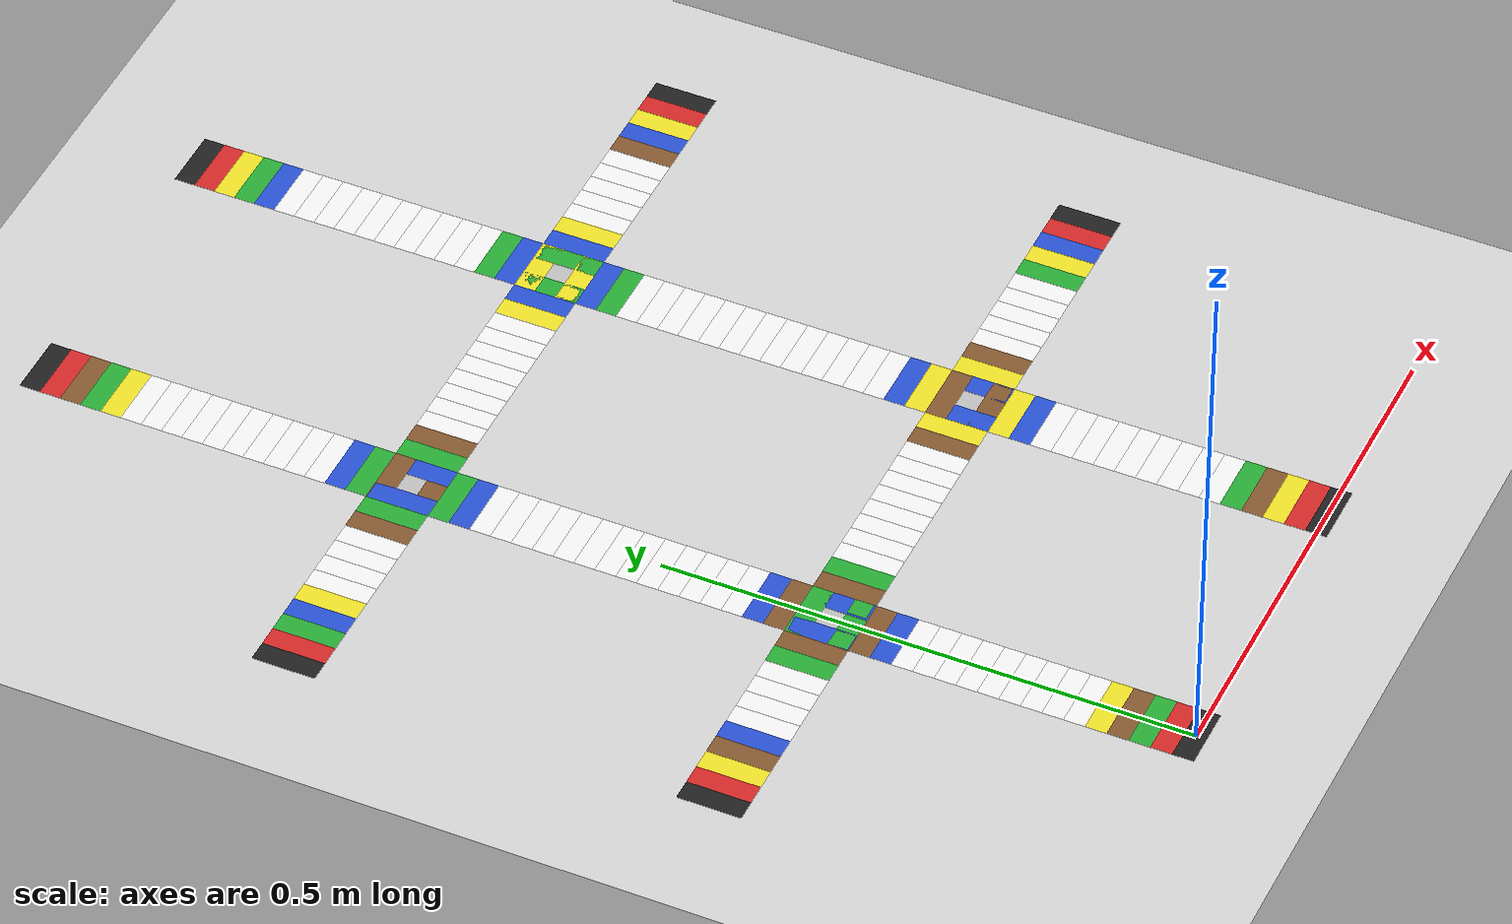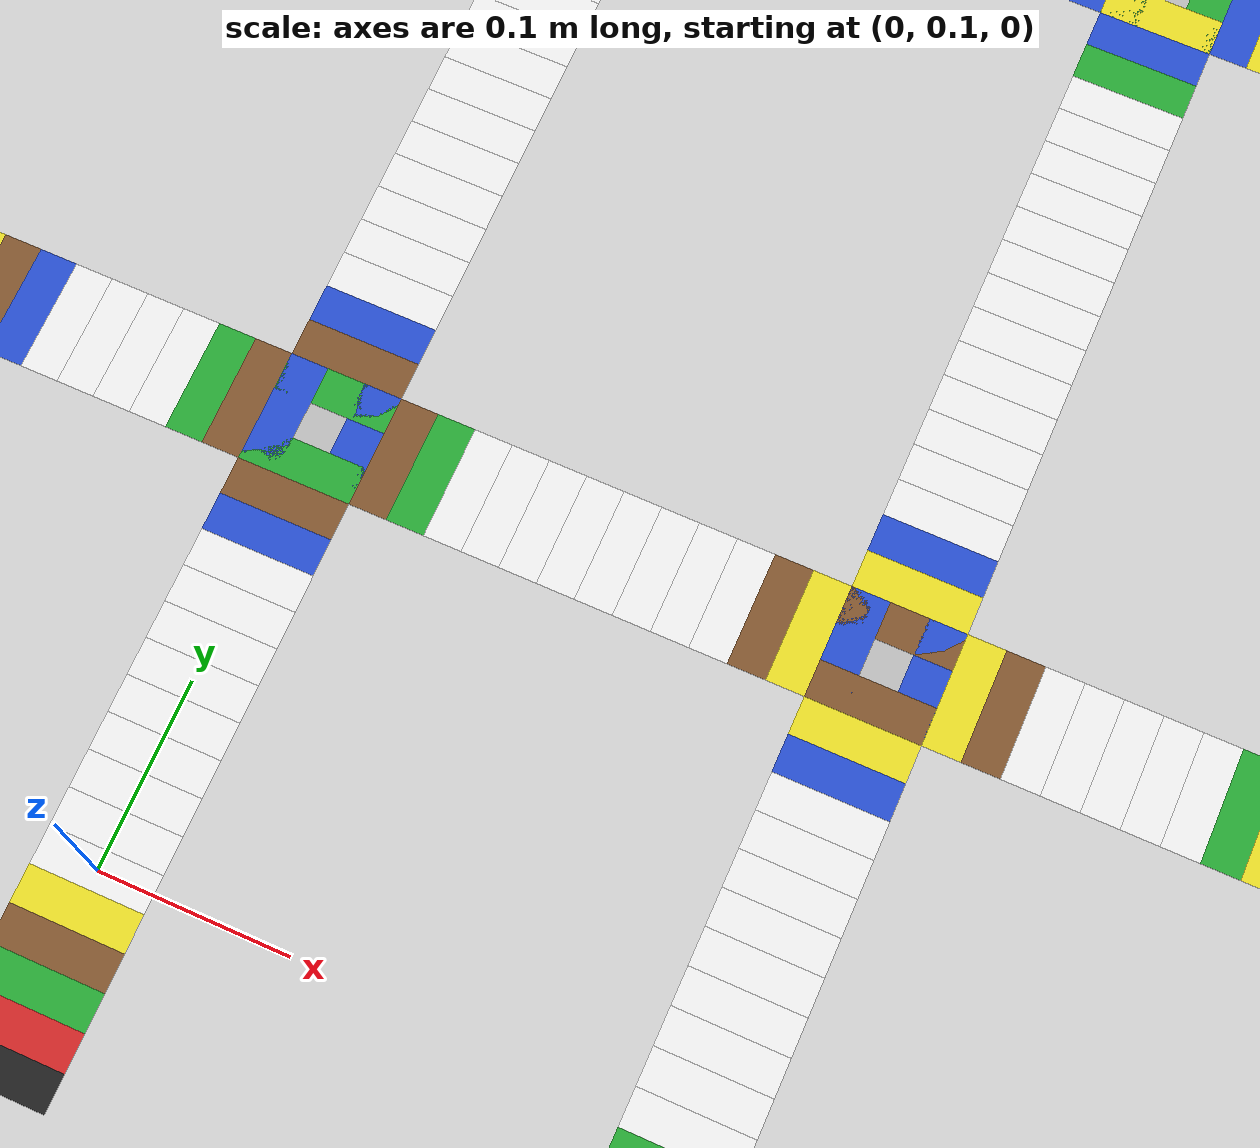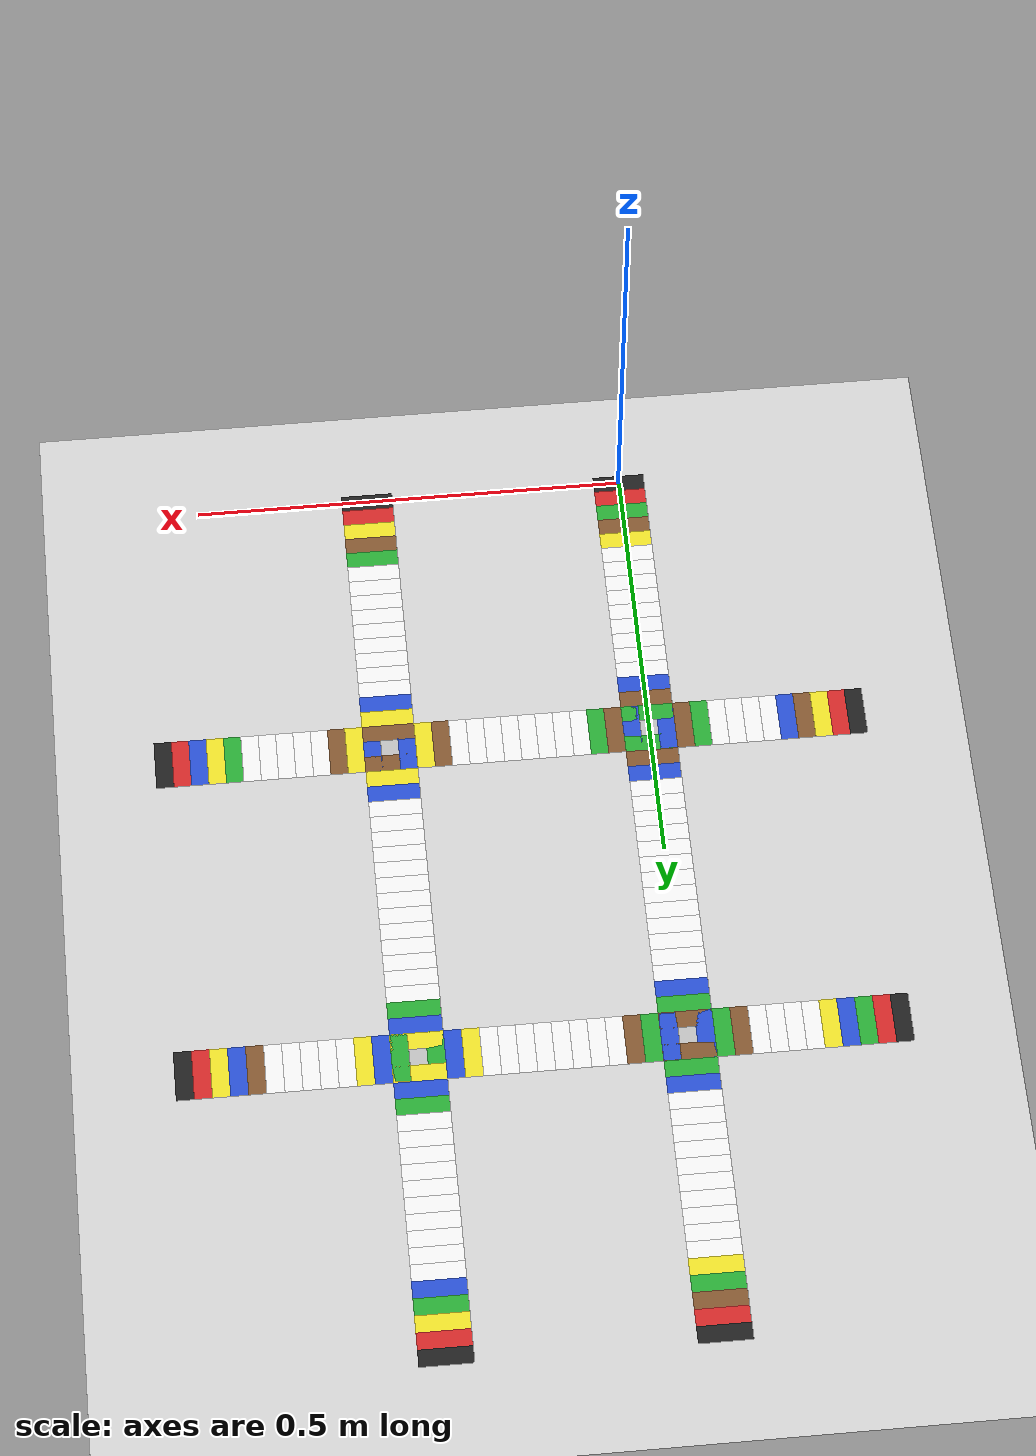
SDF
<sdf version="1.6">
 <world name="maskor_ev3_challenge">
  <model name="tileAC9">
   <pose>0 0.12 0.001 0 -0 0</pose>
   <static>1</static>
   <link name="link">
    <pose>0 0 0.001 0 -0 0</pose>
    <visual name="visual">
     <geometry><mesh><uri>model://maskor_ev3_tile/meshes/ev3_tile.dae</uri><scale>1 1 1</scale></mesh></geometry>
     <material>
      <script>
       <uri>model://maskor_ev3_tile/materials/scripts</uri>
       <uri>model://maskor_ev3_tile/materials/textures</uri>
       <name>white</name>
      </script>
     </material>
    </visual>
   </link>
  </model>
  <model name="tileAC3">
   <pose>0 0 0.001 0 -0 0</pose>
   <static>1</static>
   <link name="link">
    <pose>0 0 0.001 0 -0 0</pose>
    <visual name="visual">
     <geometry><mesh><uri>model://maskor_ev3_tile/meshes/ev3_tile.dae</uri><scale>1 1 1</scale></mesh></geometry>
     <material>
      <script>
       <uri>model://maskor_ev3_tile/materials/scripts</uri>
       <uri>model://maskor_ev3_tile/materials/textures</uri>
       <name>black</name>
      </script>
     </material>
    </visual>
   </link>
  </model>
  <model name="tileAC4">
   <pose>0 0.02 0.001 0 -0 0</pose>
   <static>1</static>
   <link name="link">
    <pose>0 0 0.001 0 -0 0</pose>
    <visual name="visual">
     <geometry><mesh><uri>model://maskor_ev3_tile/meshes/ev3_tile.dae</uri><scale>1 1 1</scale></mesh></geometry>
     <material>
      <script>
       <uri>model://maskor_ev3_tile/materials/scripts</uri>
       <uri>model://maskor_ev3_tile/materials/textures</uri>
       <name>red</name>
      </script>
     </material>
    </visual>
   </link>
  </model>
  <model name="tileAC5">
   <pose>0 0.04 0.001 0 -0 0</pose>
   <static>1</static>
   <link name="link">
    <pose>0 0 0.001 0 -0 0</pose>
    <visual name="visual">
     <geometry><mesh><uri>model://maskor_ev3_tile/meshes/ev3_tile.dae</uri><scale>1 1 1</scale></mesh></geometry>
     <material>
      <script>
       <uri>model://maskor_ev3_tile/materials/scripts</uri>
       <uri>model://maskor_ev3_tile/materials/textures</uri>
       <name>green</name>
      </script>
     </material>
    </visual>
   </link>
  </model>
  <model name="tileAC6">
   <pose>0 0.06 0.001 0 -0 0</pose>
   <static>1</static>
   <link name="link">
    <pose>0 0 0.001 0 -0 0</pose>
    <visual name="visual">
     <geometry><mesh><uri>model://maskor_ev3_tile/meshes/ev3_tile.dae</uri><scale>1 1 1</scale></mesh></geometry>
     <material>
      <script>
       <uri>model://maskor_ev3_tile/materials/scripts</uri>
       <uri>model://maskor_ev3_tile/materials/textures</uri>
       <name>brown</name>
      </script>
     </material>
    </visual>
   </link>
  </model>
  <model name="tileAC7">
   <pose>0 0.08 0.001 0 -0 0</pose>
   <static>1</static>
   <link name="link">
    <pose>0 0 0.001 0 -0 0</pose>
    <visual name="visual">
     <geometry><mesh><uri>model://maskor_ev3_tile/meshes/ev3_tile.dae</uri><scale>1 1 1</scale></mesh></geometry>
     <material>
      <script>
       <uri>model://maskor_ev3_tile/materials/scripts</uri>
       <uri>model://maskor_ev3_tile/materials/textures</uri>
       <name>yellow</name>
      </script>
     </material>
    </visual>
   </link>
  </model>
  <model name="tileAC8">
   <pose>0 0.1 0.001 0 -0 0</pose>
   <static>1</static>
   <link name="link">
    <pose>0 0 0.001 0 -0 0</pose>
    <visual name="visual">
     <geometry><mesh><uri>model://maskor_ev3_tile/meshes/ev3_tile.dae</uri><scale>1 1 1</scale></mesh></geometry>
     <material>
      <script>
       <uri>model://maskor_ev3_tile/materials/scripts</uri>
       <uri>model://maskor_ev3_tile/materials/textures</uri>
       <name>white</name>
      </script>
     </material>
    </visual>
   </link>
  </model>
  <model name="tileAC10">
   <pose>0 0.14 0.001 0 -0 0</pose>
   <static>1</static>
   <link name="link">
    <pose>0 0 0.001 0 -0 0</pose>
    <visual name="visual">
     <geometry><mesh><uri>model://maskor_ev3_tile/meshes/ev3_tile.dae</uri><scale>1 1 1</scale></mesh></geometry>
     <material>
      <script>
       <uri>model://maskor_ev3_tile/materials/scripts</uri>
       <uri>model://maskor_ev3_tile/materials/textures</uri>
       <name>white</name>
      </script>
     </material>
    </visual>
   </link>
  </model>
  <model name="tileAC11">
   <pose>0 0.16 0.001 0 -0 0</pose>
   <static>1</static>
   <link name="link">
    <pose>0 0 0.001 0 -0 0</pose>
    <visual name="visual">
     <geometry><mesh><uri>model://maskor_ev3_tile/meshes/ev3_tile.dae</uri><scale>1 1 1</scale></mesh></geometry>
     <material>
      <script>
       <uri>model://maskor_ev3_tile/materials/scripts</uri>
       <uri>model://maskor_ev3_tile/materials/textures</uri>
       <name>white</name>
      </script>
     </material>
    </visual>
   </link>
  </model>
  <model name="tileAC12">
   <pose>0 0.18 0.001 0 -0 0</pose>
   <static>1</static>
   <link name="link">
    <pose>0 0 0.001 0 -0 0</pose>
    <visual name="visual">
     <geometry><mesh><uri>model://maskor_ev3_tile/meshes/ev3_tile.dae</uri><scale>1 1 1</scale></mesh></geometry>
     <material>
      <script>
       <uri>model://maskor_ev3_tile/materials/scripts</uri>
       <uri>model://maskor_ev3_tile/materials/textures</uri>
       <name>white</name>
      </script>
     </material>
    </visual>
   </link>
  </model>
  <model name="tileAC13">
   <pose>0 0.2 0.001 0 -0 0</pose>
   <static>1</static>
   <link name="link">
    <pose>0 0 0.001 0 -0 0</pose>
    <visual name="visual">
     <geometry><mesh><uri>model://maskor_ev3_tile/meshes/ev3_tile.dae</uri><scale>1 1 1</scale></mesh></geometry>
     <material>
      <script>
       <uri>model://maskor_ev3_tile/materials/scripts</uri>
       <uri>model://maskor_ev3_tile/materials/textures</uri>
       <name>white</name>
      </script>
     </material>
    </visual>
   </link>
  </model>
  <model name="tileAC14">
   <pose>0 0.22 0.001 0 -0 0</pose>
   <static>1</static>
   <link name="link">
    <pose>0 0 0.001 0 -0 0</pose>
    <visual name="visual">
     <geometry><mesh><uri>model://maskor_ev3_tile/meshes/ev3_tile.dae</uri><scale>1 1 1</scale></mesh></geometry>
     <material>
      <script>
       <uri>model://maskor_ev3_tile/materials/scripts</uri>
       <uri>model://maskor_ev3_tile/materials/textures</uri>
       <name>white</name>
      </script>
     </material>
    </visual>
   </link>
  </model>
  <model name="tileAC15">
   <pose>0 0.24 0.001 0 -0 0</pose>
   <static>1</static>
   <link name="link">
    <pose>0 0 0.001 0 -0 0</pose>
    <visual name="visual">
     <geometry><mesh><uri>model://maskor_ev3_tile/meshes/ev3_tile.dae</uri><scale>1 1 1</scale></mesh></geometry>
     <material>
      <script>
       <uri>model://maskor_ev3_tile/materials/scripts</uri>
       <uri>model://maskor_ev3_tile/materials/textures</uri>
       <name>white</name>
      </script>
     </material>
    </visual>
   </link>
  </model>
  <model name="tileAC16">
   <pose>0 0.26 0.001 0 -0 0</pose>
   <static>1</static>
   <link name="link">
    <pose>0 0 0.001 0 -0 0</pose>
    <visual name="visual">
     <geometry><mesh><uri>model://maskor_ev3_tile/meshes/ev3_tile.dae</uri><scale>1 1 1</scale></mesh></geometry>
     <material>
      <script>
       <uri>model://maskor_ev3_tile/materials/scripts</uri>
       <uri>model://maskor_ev3_tile/materials/textures</uri>
       <name>white</name>
      </script>
     </material>
    </visual>
   </link>
  </model>
  <model name="tileAC17">
   <pose>0 0.28 0.001 0 -0 0</pose>
   <static>1</static>
   <link name="link">
    <pose>0 0 0.001 0 -0 0</pose>
    <visual name="visual">
     <geometry><mesh><uri>model://maskor_ev3_tile/meshes/ev3_tile.dae</uri><scale>1 1 1</scale></mesh></geometry>
     <material>
      <script>
       <uri>model://maskor_ev3_tile/materials/scripts</uri>
       <uri>model://maskor_ev3_tile/materials/textures</uri>
       <name>blue</name>
      </script>
     </material>
    </visual>
   </link>
  </model>
  <model name="tileAC18">
   <pose>0 0.3 0.001 0 -0 0</pose>
   <static>1</static>
   <link name="link">
    <pose>0 0 0.001 0 -0 0</pose>
    <visual name="visual">
     <geometry><mesh><uri>model://maskor_ev3_tile/meshes/ev3_tile.dae</uri><scale>1 1 1</scale></mesh></geometry>
     <material>
      <script>
       <uri>model://maskor_ev3_tile/materials/scripts</uri>
       <uri>model://maskor_ev3_tile/materials/textures</uri>
       <name>brown</name>
      </script>
     </material>
    </visual>
   </link>
  </model>
  <model name="tileAC19">
   <pose>0 0.32 0.001 0 -0 0</pose>
   <static>1</static>
   <link name="link">
    <pose>0 0 0.001 0 -0 0</pose>
    <visual name="visual">
     <geometry><mesh><uri>model://maskor_ev3_tile/meshes/ev3_tile.dae</uri><scale>1 1 1</scale></mesh></geometry>
     <material>
      <script>
       <uri>model://maskor_ev3_tile/materials/scripts</uri>
       <uri>model://maskor_ev3_tile/materials/textures</uri>
       <name>green</name>
      </script>
     </material>
    </visual>
   </link>
  </model>
  <model name="tileAC20">
   <pose>0 0.34 0.002 0 -0 0</pose>
   <static>1</static>
   <link name="link">
    <visual name="visual">
     <geometry>
      <mesh><uri>model://maskor_ev3_tile_center/meshes/ev3_tile_center.dae</uri><scale>1 1 1</scale></mesh>
     </geometry>
     <material>
      <script>
       <uri>model://maskor_ev3_tile_center/materials/scripts</uri>
       <uri>model://maskor_ev3_tile_center/materials/textures</uri>
       <name>center</name>
      </script>
     </material>
    </visual>
   </link>
  </model>
  <model name="tileAC21">
   <pose>0 0.36 0.001 0 -0 0</pose>
   <static>1</static>
   <link name="link">
    <pose>0 0 0.001 0 -0 0</pose>
    <visual name="visual">
     <geometry><mesh><uri>model://maskor_ev3_tile/meshes/ev3_tile.dae</uri><scale>1 1 1</scale></mesh></geometry>
     <material>
      <script>
       <uri>model://maskor_ev3_tile/materials/scripts</uri>
       <uri>model://maskor_ev3_tile/materials/textures</uri>
       <name>green</name>
      </script>
     </material>
    </visual>
   </link>
  </model>
  <model name="tileAC22">
   <pose>0 0.38 0.001 0 -0 0</pose>
   <static>1</static>
   <link name="link">
    <pose>0 0 0.001 0 -0 0</pose>
    <visual name="visual">
     <geometry><mesh><uri>model://maskor_ev3_tile/meshes/ev3_tile.dae</uri><scale>1 1 1</scale></mesh></geometry>
     <material>
      <script>
       <uri>model://maskor_ev3_tile/materials/scripts</uri>
       <uri>model://maskor_ev3_tile/materials/textures</uri>
       <name>brown</name>
      </script>
     </material>
    </visual>
   </link>
  </model>
  <model name="tileAC23">
   <pose>0 0.4 0.001 0 -0 0</pose>
   <static>1</static>
   <link name="link">
    <pose>0 0 0.001 0 -0 0</pose>
    <visual name="visual">
     <geometry><mesh><uri>model://maskor_ev3_tile/meshes/ev3_tile.dae</uri><scale>1 1 1</scale></mesh></geometry>
     <material>
      <script>
       <uri>model://maskor_ev3_tile/materials/scripts</uri>
       <uri>model://maskor_ev3_tile/materials/textures</uri>
       <name>blue</name>
      </script>
     </material>
    </visual>
   </link>
  </model>
  <model name="tileAC24">
   <pose>0 0.42 0.001 0 -0 0</pose>
   <static>1</static>
   <link name="link">
    <pose>0 0 0.001 0 -0 0</pose>
    <visual name="visual">
     <geometry><mesh><uri>model://maskor_ev3_tile/meshes/ev3_tile.dae</uri><scale>1 1 1</scale></mesh></geometry>
     <material>
      <script>
       <uri>model://maskor_ev3_tile/materials/scripts</uri>
       <uri>model://maskor_ev3_tile/materials/textures</uri>
       <name>white</name>
      </script>
     </material>
    </visual>
   </link>
  </model>
  <model name="tileAC25">
   <pose>0 0.44 0.001 0 -0 0</pose>
   <static>1</static>
   <link name="link">
    <pose>0 0 0.001 0 -0 0</pose>
    <visual name="visual">
     <geometry><mesh><uri>model://maskor_ev3_tile/meshes/ev3_tile.dae</uri><scale>1 1 1</scale></mesh></geometry>
     <material>
      <script>
       <uri>model://maskor_ev3_tile/materials/scripts</uri>
       <uri>model://maskor_ev3_tile/materials/textures</uri>
       <name>white</name>
      </script>
     </material>
    </visual>
   </link>
  </model>
  <model name="tileAC26">
   <pose>0 0.46 0.001 0 -0 0</pose>
   <static>1</static>
   <link name="link">
    <pose>0 0 0.001 0 -0 0</pose>
    <visual name="visual">
     <geometry><mesh><uri>model://maskor_ev3_tile/meshes/ev3_tile.dae</uri><scale>1 1 1</scale></mesh></geometry>
     <material>
      <script>
       <uri>model://maskor_ev3_tile/materials/scripts</uri>
       <uri>model://maskor_ev3_tile/materials/textures</uri>
       <name>white</name>
      </script>
     </material>
    </visual>
   </link>
  </model>
  <model name="tileAC27">
   <pose>0 0.48 0.001 0 -0 0</pose>
   <static>1</static>
   <link name="link">
    <pose>0 0 0.001 0 -0 0</pose>
    <visual name="visual">
     <geometry><mesh><uri>model://maskor_ev3_tile/meshes/ev3_tile.dae</uri><scale>1 1 1</scale></mesh></geometry>
     <material>
      <script>
       <uri>model://maskor_ev3_tile/materials/scripts</uri>
       <uri>model://maskor_ev3_tile/materials/textures</uri>
       <name>white</name>
      </script>
     </material>
    </visual>
   </link>
  </model>
  <model name="tileAC34">
   <pose>0 0.62 0.001 0 -0 0</pose>
   <static>1</static>
   <link name="link">
    <pose>0 0 0.001 0 -0 0</pose>
    <visual name="visual">
     <geometry><mesh><uri>model://maskor_ev3_tile/meshes/ev3_tile.dae</uri><scale>1 1 1</scale></mesh></geometry>
     <material>
      <script>
       <uri>model://maskor_ev3_tile/materials/scripts</uri>
       <uri>model://maskor_ev3_tile/materials/textures</uri>
       <name>white</name>
      </script>
     </material>
    </visual>
   </link>
  </model>
  <model name="tileAC28">
   <pose>0 0.5 0.001 0 -0 0</pose>
   <static>1</static>
   <link name="link">
    <pose>0 0 0.001 0 -0 0</pose>
    <visual name="visual">
     <geometry><mesh><uri>model://maskor_ev3_tile/meshes/ev3_tile.dae</uri><scale>1 1 1</scale></mesh></geometry>
     <material>
      <script>
       <uri>model://maskor_ev3_tile/materials/scripts</uri>
       <uri>model://maskor_ev3_tile/materials/textures</uri>
       <name>white</name>
      </script>
     </material>
    </visual>
   </link>
  </model>
  <model name="tileAC29">
   <pose>0 0.52 0.001 0 -0 0</pose>
   <static>1</static>
   <link name="link">
    <pose>0 0 0.001 0 -0 0</pose>
    <visual name="visual">
     <geometry><mesh><uri>model://maskor_ev3_tile/meshes/ev3_tile.dae</uri><scale>1 1 1</scale></mesh></geometry>
     <material>
      <script>
       <uri>model://maskor_ev3_tile/materials/scripts</uri>
       <uri>model://maskor_ev3_tile/materials/textures</uri>
       <name>white</name>
      </script>
     </material>
    </visual>
   </link>
  </model>
  <model name="tileAC30">
   <pose>0 0.54 0.001 0 -0 0</pose>
   <static>1</static>
   <link name="link">
    <pose>0 0 0.001 0 -0 0</pose>
    <visual name="visual">
     <geometry><mesh><uri>model://maskor_ev3_tile/meshes/ev3_tile.dae</uri><scale>1 1 1</scale></mesh></geometry>
     <material>
      <script>
       <uri>model://maskor_ev3_tile/materials/scripts</uri>
       <uri>model://maskor_ev3_tile/materials/textures</uri>
       <name>white</name>
      </script>
     </material>
    </visual>
   </link>
  </model>
  <model name="tileAC31">
   <pose>0 0.56 0.001 0 -0 0</pose>
   <static>1</static>
   <link name="link">
    <pose>0 0 0.001 0 -0 0</pose>
    <visual name="visual">
     <geometry><mesh><uri>model://maskor_ev3_tile/meshes/ev3_tile.dae</uri><scale>1 1 1</scale></mesh></geometry>
     <material>
      <script>
       <uri>model://maskor_ev3_tile/materials/scripts</uri>
       <uri>model://maskor_ev3_tile/materials/textures</uri>
       <name>white</name>
      </script>
     </material>
    </visual>
   </link>
  </model>
  <model name="tileAC32">
   <pose>0 0.58 0.001 0 -0 0</pose>
   <static>1</static>
   <link name="link">
    <pose>0 0 0.001 0 -0 0</pose>
    <visual name="visual">
     <geometry><mesh><uri>model://maskor_ev3_tile/meshes/ev3_tile.dae</uri><scale>1 1 1</scale></mesh></geometry>
     <material>
      <script>
       <uri>model://maskor_ev3_tile/materials/scripts</uri>
       <uri>model://maskor_ev3_tile/materials/textures</uri>
       <name>white</name>
      </script>
     </material>
    </visual>
   </link>
  </model>
  <model name="tileAC33">
   <pose>0 0.6 0.001 0 -0 0</pose>
   <static>1</static>
   <link name="link">
    <pose>0 0 0.001 0 -0 0</pose>
    <visual name="visual">
     <geometry><mesh><uri>model://maskor_ev3_tile/meshes/ev3_tile.dae</uri><scale>1 1 1</scale></mesh></geometry>
     <material>
      <script>
       <uri>model://maskor_ev3_tile/materials/scripts</uri>
       <uri>model://maskor_ev3_tile/materials/textures</uri>
       <name>white</name>
      </script>
     </material>
    </visual>
   </link>
  </model>
  <model name="tileAC35">
   <pose>0 0.64 0.001 0 -0 0</pose>
   <static>1</static>
   <link name="link">
    <pose>0 0 0.001 0 -0 0</pose>
    <visual name="visual">
     <geometry><mesh><uri>model://maskor_ev3_tile/meshes/ev3_tile.dae</uri><scale>1 1 1</scale></mesh></geometry>
     <material>
      <script>
       <uri>model://maskor_ev3_tile/materials/scripts</uri>
       <uri>model://maskor_ev3_tile/materials/textures</uri>
       <name>white</name>
      </script>
     </material>
    </visual>
   </link>
  </model>
  <model name="tileAC36">
   <pose>0 0.66 0.001 0 -0 0</pose>
   <static>1</static>
   <link name="link">
    <pose>0 0 0.001 0 -0 0</pose>
    <visual name="visual">
     <geometry><mesh><uri>model://maskor_ev3_tile/meshes/ev3_tile.dae</uri><scale>1 1 1</scale></mesh></geometry>
     <material>
      <script>
       <uri>model://maskor_ev3_tile/materials/scripts</uri>
       <uri>model://maskor_ev3_tile/materials/textures</uri>
       <name>white</name>
      </script>
     </material>
    </visual>
   </link>
  </model>
  <model name="tileAC37">
   <pose>0 0.68 0.001 0 -0 0</pose>
   <static>1</static>
   <link name="link">
    <pose>0 0 0.001 0 -0 0</pose>
    <visual name="visual">
     <geometry><mesh><uri>model://maskor_ev3_tile/meshes/ev3_tile.dae</uri><scale>1 1 1</scale></mesh></geometry>
     <material>
      <script>
       <uri>model://maskor_ev3_tile/materials/scripts</uri>
       <uri>model://maskor_ev3_tile/materials/textures</uri>
       <name>blue</name>
      </script>
     </material>
    </visual>
   </link>
  </model>
  <model name="tileAC38">
   <pose>0 0.7 0.001 0 -0 0</pose>
   <static>1</static>
   <link name="link">
    <pose>0 0 0.001 0 -0 0</pose>
    <visual name="visual">
     <geometry><mesh><uri>model://maskor_ev3_tile/meshes/ev3_tile.dae</uri><scale>1 1 1</scale></mesh></geometry>
     <material>
      <script>
       <uri>model://maskor_ev3_tile/materials/scripts</uri>
       <uri>model://maskor_ev3_tile/materials/textures</uri>
       <name>green</name>
      </script>
     </material>
    </visual>
   </link>
  </model>
  <model name="tileAC39">
   <pose>0 0.72 0.001 0 -0 0</pose>
   <static>1</static>
   <link name="link">
    <pose>0 0 0.001 0 -0 0</pose>
    <visual name="visual">
     <geometry><mesh><uri>model://maskor_ev3_tile/meshes/ev3_tile.dae</uri><scale>1 1 1</scale></mesh></geometry>
     <material>
      <script>
       <uri>model://maskor_ev3_tile/materials/scripts</uri>
       <uri>model://maskor_ev3_tile/materials/textures</uri>
       <name>brown</name>
      </script>
     </material>
    </visual>
   </link>
  </model>
  <model name="tileAC40">
   <pose>0 0.74 0.002 0 -0 0</pose>
   <static>1</static>
   <link name="link">
    <visual name="visual">
     <geometry>
      <mesh><uri>model://maskor_ev3_tile_center/meshes/ev3_tile_center.dae</uri><scale>1 1 1</scale></mesh>
     </geometry>
     <material>
      <script>
       <uri>model://maskor_ev3_tile_center/materials/scripts</uri>
       <uri>model://maskor_ev3_tile_center/materials/textures</uri>
       <name>center</name>
      </script>
     </material>
    </visual>
   </link>
  </model>
  <model name="tileAC41">
   <pose>0 0.76 0.001 0 -0 0</pose>
   <static>1</static>
   <link name="link">
    <pose>0 0 0.001 0 -0 0</pose>
    <visual name="visual">
     <geometry><mesh><uri>model://maskor_ev3_tile/meshes/ev3_tile.dae</uri><scale>1 1 1</scale></mesh></geometry>
     <material>
      <script>
       <uri>model://maskor_ev3_tile/materials/scripts</uri>
       <uri>model://maskor_ev3_tile/materials/textures</uri>
       <name>brown</name>
      </script>
     </material>
    </visual>
   </link>
  </model>
  <model name="tileAC42">
   <pose>0 0.78 0.001 0 -0 0</pose>
   <static>1</static>
   <link name="link">
    <pose>0 0 0.001 0 -0 0</pose>
    <visual name="visual">
     <geometry><mesh><uri>model://maskor_ev3_tile/meshes/ev3_tile.dae</uri><scale>1 1 1</scale></mesh></geometry>
     <material>
      <script>
       <uri>model://maskor_ev3_tile/materials/scripts</uri>
       <uri>model://maskor_ev3_tile/materials/textures</uri>
       <name>green</name>
      </script>
     </material>
    </visual>
   </link>
  </model>
  <model name="tileAC43">
   <pose>0 0.8 0.001 0 -0 0</pose>
   <static>1</static>
   <link name="link">
    <pose>0 0 0.001 0 -0 0</pose>
    <visual name="visual">
     <geometry><mesh><uri>model://maskor_ev3_tile/meshes/ev3_tile.dae</uri><scale>1 1 1</scale></mesh></geometry>
     <material>
      <script>
       <uri>model://maskor_ev3_tile/materials/scripts</uri>
       <uri>model://maskor_ev3_tile/materials/textures</uri>
       <name>blue</name>
      </script>
     </material>
    </visual>
   </link>
  </model>
  <model name="tileAC44">
   <pose>0 0.82 0.001 0 -0 0</pose>
   <static>1</static>
   <link name="link">
    <pose>0 0 0.001 0 -0 0</pose>
    <visual name="visual">
     <geometry><mesh><uri>model://maskor_ev3_tile/meshes/ev3_tile.dae</uri><scale>1 1 1</scale></mesh></geometry>
     <material>
      <script>
       <uri>model://maskor_ev3_tile/materials/scripts</uri>
       <uri>model://maskor_ev3_tile/materials/textures</uri>
       <name>white</name>
      </script>
     </material>
    </visual>
   </link>
  </model>
  <model name="tileAC45">
   <pose>0 0.84 0.001 0 -0 0</pose>
   <static>1</static>
   <link name="link">
    <pose>0 0 0.001 0 -0 0</pose>
    <visual name="visual">
     <geometry><mesh><uri>model://maskor_ev3_tile/meshes/ev3_tile.dae</uri><scale>1 1 1</scale></mesh></geometry>
     <material>
      <script>
       <uri>model://maskor_ev3_tile/materials/scripts</uri>
       <uri>model://maskor_ev3_tile/materials/textures</uri>
       <name>white</name>
      </script>
     </material>
    </visual>
   </link>
  </model>
  <model name="tileAC46">
   <pose>0 0.86 0.001 0 -0 0</pose>
   <static>1</static>
   <link name="link">
    <pose>0 0 0.001 0 -0 0</pose>
    <visual name="visual">
     <geometry><mesh><uri>model://maskor_ev3_tile/meshes/ev3_tile.dae</uri><scale>1 1 1</scale></mesh></geometry>
     <material>
      <script>
       <uri>model://maskor_ev3_tile/materials/scripts</uri>
       <uri>model://maskor_ev3_tile/materials/textures</uri>
       <name>white</name>
      </script>
     </material>
    </visual>
   </link>
  </model>
  <model name="tileAC47">
   <pose>0 0.88 0.001 0 -0 0</pose>
   <static>1</static>
   <link name="link">
    <pose>0 0 0.001 0 -0 0</pose>
    <visual name="visual">
     <geometry><mesh><uri>model://maskor_ev3_tile/meshes/ev3_tile.dae</uri><scale>1 1 1</scale></mesh></geometry>
     <material>
      <script>
       <uri>model://maskor_ev3_tile/materials/scripts</uri>
       <uri>model://maskor_ev3_tile/materials/textures</uri>
       <name>white</name>
      </script>
     </material>
    </visual>
   </link>
  </model>
  <model name="tileAC48">
   <pose>0 0.9 0.001 0 -0 0</pose>
   <static>1</static>
   <link name="link">
    <pose>0 0 0.001 0 -0 0</pose>
    <visual name="visual">
     <geometry><mesh><uri>model://maskor_ev3_tile/meshes/ev3_tile.dae</uri><scale>1 1 1</scale></mesh></geometry>
     <material>
      <script>
       <uri>model://maskor_ev3_tile/materials/scripts</uri>
       <uri>model://maskor_ev3_tile/materials/textures</uri>
       <name>white</name>
      </script>
     </material>
    </visual>
   </link>
  </model>
  <model name="tileAC49">
   <pose>0 0.92 0.001 0 -0 0</pose>
   <static>1</static>
   <link name="link">
    <pose>0 0 0.001 0 -0 0</pose>
    <visual name="visual">
     <geometry><mesh><uri>model://maskor_ev3_tile/meshes/ev3_tile.dae</uri><scale>1 1 1</scale></mesh></geometry>
     <material>
      <script>
       <uri>model://maskor_ev3_tile/materials/scripts</uri>
       <uri>model://maskor_ev3_tile/materials/textures</uri>
       <name>white</name>
      </script>
     </material>
    </visual>
   </link>
  </model>
  <model name="tileAC50">
   <pose>0 0.94 0.001 0 -0 0</pose>
   <static>1</static>
   <link name="link">
    <pose>0 0 0.001 0 -0 0</pose>
    <visual name="visual">
     <geometry><mesh><uri>model://maskor_ev3_tile/meshes/ev3_tile.dae</uri><scale>1 1 1</scale></mesh></geometry>
     <material>
      <script>
       <uri>model://maskor_ev3_tile/materials/scripts</uri>
       <uri>model://maskor_ev3_tile/materials/textures</uri>
       <name>white</name>
      </script>
     </material>
    </visual>
   </link>
  </model>
  <model name="tileAC51">
   <pose>0 0.96 0.001 0 -0 0</pose>
   <static>1</static>
   <link name="link">
    <pose>0 0 0.001 0 -0 0</pose>
    <visual name="visual">
     <geometry><mesh><uri>model://maskor_ev3_tile/meshes/ev3_tile.dae</uri><scale>1 1 1</scale></mesh></geometry>
     <material>
      <script>
       <uri>model://maskor_ev3_tile/materials/scripts</uri>
       <uri>model://maskor_ev3_tile/materials/textures</uri>
       <name>white</name>
      </script>
     </material>
    </visual>
   </link>
  </model>
  <model name="tileAC52">
   <pose>0 0.98 0.001 0 -0 0</pose>
   <static>1</static>
   <link name="link">
    <pose>0 0 0.001 0 -0 0</pose>
    <visual name="visual">
     <geometry><mesh><uri>model://maskor_ev3_tile/meshes/ev3_tile.dae</uri><scale>1 1 1</scale></mesh></geometry>
     <material>
      <script>
       <uri>model://maskor_ev3_tile/materials/scripts</uri>
       <uri>model://maskor_ev3_tile/materials/textures</uri>
       <name>white</name>
      </script>
     </material>
    </visual>
   </link>
  </model>
  <model name="tileAC53">
   <pose>0 1 0.001 0 -0 0</pose>
   <static>1</static>
   <link name="link">
    <pose>0 0 0.001 0 -0 0</pose>
    <visual name="visual">
     <geometry><mesh><uri>model://maskor_ev3_tile/meshes/ev3_tile.dae</uri><scale>1 1 1</scale></mesh></geometry>
     <material>
      <script>
       <uri>model://maskor_ev3_tile/materials/scripts</uri>
       <uri>model://maskor_ev3_tile/materials/textures</uri>
       <name>white</name>
      </script>
     </material>
    </visual>
   </link>
  </model>
  <model name="tileAC54">
   <pose>0 1.02 0.001 0 -0 0</pose>
   <static>1</static>
   <link name="link">
    <pose>0 0 0.001 0 -0 0</pose>
    <visual name="visual">
     <geometry><mesh><uri>model://maskor_ev3_tile/meshes/ev3_tile.dae</uri><scale>1 1 1</scale></mesh></geometry>
     <material>
      <script>
       <uri>model://maskor_ev3_tile/materials/scripts</uri>
       <uri>model://maskor_ev3_tile/materials/textures</uri>
       <name>yellow</name>
      </script>
     </material>
    </visual>
   </link>
  </model>
  <model name="tileAC55">
   <pose>0 1.04 0.001 0 -0 0</pose>
   <static>1</static>
   <link name="link">
    <pose>0 0 0.001 0 -0 0</pose>
    <visual name="visual">
     <geometry><mesh><uri>model://maskor_ev3_tile/meshes/ev3_tile.dae</uri><scale>1 1 1</scale></mesh></geometry>
     <material>
      <script>
       <uri>model://maskor_ev3_tile/materials/scripts</uri>
       <uri>model://maskor_ev3_tile/materials/textures</uri>
       <name>green</name>
      </script>
     </material>
    </visual>
   </link>
  </model>
  <model name="tileAC56">
   <pose>0 1.06 0.001 0 -0 0</pose>
   <static>1</static>
   <link name="link">
    <pose>0 0 0.001 0 -0 0</pose>
    <visual name="visual">
     <geometry><mesh><uri>model://maskor_ev3_tile/meshes/ev3_tile.dae</uri><scale>1 1 1</scale></mesh></geometry>
     <material>
      <script>
       <uri>model://maskor_ev3_tile/materials/scripts</uri>
       <uri>model://maskor_ev3_tile/materials/textures</uri>
       <name>brown</name>
      </script>
     </material>
    </visual>
   </link>
  </model>
  <model name="tileAC57">
   <pose>0 1.08 0.001 0 -0 0</pose>
   <static>1</static>
   <link name="link">
    <pose>0 0 0.001 0 -0 0</pose>
    <visual name="visual">
     <geometry><mesh><uri>model://maskor_ev3_tile/meshes/ev3_tile.dae</uri><scale>1 1 1</scale></mesh></geometry>
     <material>
      <script>
       <uri>model://maskor_ev3_tile/materials/scripts</uri>
       <uri>model://maskor_ev3_tile/materials/textures</uri>
       <name>red</name>
      </script>
     </material>
    </visual>
   </link>
  </model>
  <model name="tileAC58">
   <pose>0 1.1 0.001 0 -0 0</pose>
   <static>1</static>
   <link name="link">
    <pose>0 0 0.001 0 -0 0</pose>
    <visual name="visual">
     <geometry><mesh><uri>model://maskor_ev3_tile/meshes/ev3_tile.dae</uri><scale>1 1 1</scale></mesh></geometry>
     <material>
      <script>
       <uri>model://maskor_ev3_tile/materials/scripts</uri>
       <uri>model://maskor_ev3_tile/materials/textures</uri>
       <name>black</name>
      </script>
     </material>
    </visual>
   </link>
  </model>
  <model name="tileBD3">
   <pose>0.3 0 0.001 0 -0 0</pose>
   <static>1</static>
   <link name="link">
    <pose>0 0 0.001 0 -0 0</pose>
    <visual name="visual">
     <geometry><mesh><uri>model://maskor_ev3_tile/meshes/ev3_tile.dae</uri><scale>1 1 1</scale></mesh></geometry>
     <material>
      <script>
       <uri>model://maskor_ev3_tile/materials/scripts</uri>
       <uri>model://maskor_ev3_tile/materials/textures</uri>
       <name>black</name>
      </script>
     </material>
    </visual>
   </link>
  </model>
  <model name="tileBD4">
   <pose>0.3 0.02 0.001 0 -0 0</pose>
   <static>1</static>
   <link name="link">
    <pose>0 0 0.001 0 -0 0</pose>
    <visual name="visual">
     <geometry><mesh><uri>model://maskor_ev3_tile/meshes/ev3_tile.dae</uri><scale>1 1 1</scale></mesh></geometry>
     <material>
      <script>
       <uri>model://maskor_ev3_tile/materials/scripts</uri>
       <uri>model://maskor_ev3_tile/materials/textures</uri>
       <name>red</name>
      </script>
     </material>
    </visual>
   </link>
  </model>
  <model name="tileBD5">
   <pose>0.3 0.04 0.001 0 -0 0</pose>
   <static>1</static>
   <link name="link">
    <pose>0 0 0.001 0 -0 0</pose>
    <visual name="visual">
     <geometry><mesh><uri>model://maskor_ev3_tile/meshes/ev3_tile.dae</uri><scale>1 1 1</scale></mesh></geometry>
     <material>
      <script>
       <uri>model://maskor_ev3_tile/materials/scripts</uri>
       <uri>model://maskor_ev3_tile/materials/textures</uri>
       <name>yellow</name>
      </script>
     </material>
    </visual>
   </link>
  </model>
  <model name="tileBD6">
   <pose>0.3 0.06 0.001 0 -0 0</pose>
   <static>1</static>
   <link name="link">
    <pose>0 0 0.001 0 -0 0</pose>
    <visual name="visual">
     <geometry><mesh><uri>model://maskor_ev3_tile/meshes/ev3_tile.dae</uri><scale>1 1 1</scale></mesh></geometry>
     <material>
      <script>
       <uri>model://maskor_ev3_tile/materials/scripts</uri>
       <uri>model://maskor_ev3_tile/materials/textures</uri>
       <name>brown</name>
      </script>
     </material>
    </visual>
   </link>
  </model>
  <model name="tileBD21">
   <pose>0.3 0.36 0.001 0 -0 0</pose>
   <static>1</static>
   <link name="link">
    <pose>0 0 0.001 0 -0 0</pose>
    <visual name="visual">
     <geometry><mesh><uri>model://maskor_ev3_tile/meshes/ev3_tile.dae</uri><scale>1 1 1</scale></mesh></geometry>
     <material>
      <script>
       <uri>model://maskor_ev3_tile/materials/scripts</uri>
       <uri>model://maskor_ev3_tile/materials/textures</uri>
       <name>brown</name>
      </script>
     </material>
    </visual>
   </link>
  </model>
  <model name="tileBD7">
   <pose>0.3 0.08 0.001 0 -0 0</pose>
   <static>1</static>
   <link name="link">
    <pose>0 0 0.001 0 -0 0</pose>
    <visual name="visual">
     <geometry><mesh><uri>model://maskor_ev3_tile/meshes/ev3_tile.dae</uri><scale>1 1 1</scale></mesh></geometry>
     <material>
      <script>
       <uri>model://maskor_ev3_tile/materials/scripts</uri>
       <uri>model://maskor_ev3_tile/materials/textures</uri>
       <name>green</name>
      </script>
     </material>
    </visual>
   </link>
  </model>
  <model name="tileBD8">
   <pose>0.3 0.1 0.001 0 -0 0</pose>
   <static>1</static>
   <link name="link">
    <pose>0 0 0.001 0 -0 0</pose>
    <visual name="visual">
     <geometry><mesh><uri>model://maskor_ev3_tile/meshes/ev3_tile.dae</uri><scale>1 1 1</scale></mesh></geometry>
     <material>
      <script>
       <uri>model://maskor_ev3_tile/materials/scripts</uri>
       <uri>model://maskor_ev3_tile/materials/textures</uri>
       <name>white</name>
      </script>
     </material>
    </visual>
   </link>
  </model>
  <model name="tileBD9">
   <pose>0.3 0.12 0.001 0 -0 0</pose>
   <static>1</static>
   <link name="link">
    <pose>0 0 0.001 0 -0 0</pose>
    <visual name="visual">
     <geometry><mesh><uri>model://maskor_ev3_tile/meshes/ev3_tile.dae</uri><scale>1 1 1</scale></mesh></geometry>
     <material>
      <script>
       <uri>model://maskor_ev3_tile/materials/scripts</uri>
       <uri>model://maskor_ev3_tile/materials/textures</uri>
       <name>white</name>
      </script>
     </material>
    </visual>
   </link>
  </model>
  <model name="tileBD10">
   <pose>0.3 0.14 0.001 0 -0 0</pose>
   <static>1</static>
   <link name="link">
    <pose>0 0 0.001 0 -0 0</pose>
    <visual name="visual">
     <geometry><mesh><uri>model://maskor_ev3_tile/meshes/ev3_tile.dae</uri><scale>1 1 1</scale></mesh></geometry>
     <material>
      <script>
       <uri>model://maskor_ev3_tile/materials/scripts</uri>
       <uri>model://maskor_ev3_tile/materials/textures</uri>
       <name>white</name>
      </script>
     </material>
    </visual>
   </link>
  </model>
  <model name="tileBD11">
   <pose>0.3 0.16 0.001 0 -0 0</pose>
   <static>1</static>
   <link name="link">
    <pose>0 0 0.001 0 -0 0</pose>
    <visual name="visual">
     <geometry><mesh><uri>model://maskor_ev3_tile/meshes/ev3_tile.dae</uri><scale>1 1 1</scale></mesh></geometry>
     <material>
      <script>
       <uri>model://maskor_ev3_tile/materials/scripts</uri>
       <uri>model://maskor_ev3_tile/materials/textures</uri>
       <name>white</name>
      </script>
     </material>
    </visual>
   </link>
  </model>
  <model name="tileBD12">
   <pose>0.3 0.18 0.001 0 -0 0</pose>
   <static>1</static>
   <link name="link">
    <pose>0 0 0.001 0 -0 0</pose>
    <visual name="visual">
     <geometry><mesh><uri>model://maskor_ev3_tile/meshes/ev3_tile.dae</uri><scale>1 1 1</scale></mesh></geometry>
     <material>
      <script>
       <uri>model://maskor_ev3_tile/materials/scripts</uri>
       <uri>model://maskor_ev3_tile/materials/textures</uri>
       <name>white</name>
      </script>
     </material>
    </visual>
   </link>
  </model>
  <model name="tileBD13">
   <pose>0.3 0.2 0.001 0 -0 0</pose>
   <static>1</static>
   <link name="link">
    <pose>0 0 0.001 0 -0 0</pose>
    <visual name="visual">
     <geometry><mesh><uri>model://maskor_ev3_tile/meshes/ev3_tile.dae</uri><scale>1 1 1</scale></mesh></geometry>
     <material>
      <script>
       <uri>model://maskor_ev3_tile/materials/scripts</uri>
       <uri>model://maskor_ev3_tile/materials/textures</uri>
       <name>white</name>
      </script>
     </material>
    </visual>
   </link>
  </model>
  <model name="tileBD14">
   <pose>0.3 0.22 0.001 0 -0 0</pose>
   <static>1</static>
   <link name="link">
    <pose>0 0 0.001 0 -0 0</pose>
    <visual name="visual">
     <geometry><mesh><uri>model://maskor_ev3_tile/meshes/ev3_tile.dae</uri><scale>1 1 1</scale></mesh></geometry>
     <material>
      <script>
       <uri>model://maskor_ev3_tile/materials/scripts</uri>
       <uri>model://maskor_ev3_tile/materials/textures</uri>
       <name>white</name>
      </script>
     </material>
    </visual>
   </link>
  </model>
  <model name="tileBD15">
   <pose>0.3 0.24 0.001 0 -0 0</pose>
   <static>1</static>
   <link name="link">
    <pose>0 0 0.001 0 -0 0</pose>
    <visual name="visual">
     <geometry><mesh><uri>model://maskor_ev3_tile/meshes/ev3_tile.dae</uri><scale>1 1 1</scale></mesh></geometry>
     <material>
      <script>
       <uri>model://maskor_ev3_tile/materials/scripts</uri>
       <uri>model://maskor_ev3_tile/materials/textures</uri>
       <name>white</name>
      </script>
     </material>
    </visual>
   </link>
  </model>
  <model name="tileBD16">
   <pose>0.3 0.26 0.001 0 -0 0</pose>
   <static>1</static>
   <link name="link">
    <pose>0 0 0.001 0 -0 0</pose>
    <visual name="visual">
     <geometry><mesh><uri>model://maskor_ev3_tile/meshes/ev3_tile.dae</uri><scale>1 1 1</scale></mesh></geometry>
     <material>
      <script>
       <uri>model://maskor_ev3_tile/materials/scripts</uri>
       <uri>model://maskor_ev3_tile/materials/textures</uri>
       <name>white</name>
      </script>
     </material>
    </visual>
   </link>
  </model>
  <model name="tileBD17">
   <pose>0.3 0.28 0.001 0 -0 0</pose>
   <static>1</static>
   <link name="link">
    <pose>0 0 0.001 0 -0 0</pose>
    <visual name="visual">
     <geometry><mesh><uri>model://maskor_ev3_tile/meshes/ev3_tile.dae</uri><scale>1 1 1</scale></mesh></geometry>
     <material>
      <script>
       <uri>model://maskor_ev3_tile/materials/scripts</uri>
       <uri>model://maskor_ev3_tile/materials/textures</uri>
       <name>blue</name>
      </script>
     </material>
    </visual>
   </link>
  </model>
  <model name="tileBD18">
   <pose>0.3 0.3 0.001 0 -0 0</pose>
   <static>1</static>
   <link name="link">
    <pose>0 0 0.001 0 -0 0</pose>
    <visual name="visual">
     <geometry><mesh><uri>model://maskor_ev3_tile/meshes/ev3_tile.dae</uri><scale>1 1 1</scale></mesh></geometry>
     <material>
      <script>
       <uri>model://maskor_ev3_tile/materials/scripts</uri>
       <uri>model://maskor_ev3_tile/materials/textures</uri>
       <name>yellow</name>
      </script>
     </material>
    </visual>
   </link>
  </model>
  <model name="tileBD19">
   <pose>0.3 0.32 0.001 0 -0 0</pose>
   <static>1</static>
   <link name="link">
    <pose>0 0 0.001 0 -0 0</pose>
    <visual name="visual">
     <geometry><mesh><uri>model://maskor_ev3_tile/meshes/ev3_tile.dae</uri><scale>1 1 1</scale></mesh></geometry>
     <material>
      <script>
       <uri>model://maskor_ev3_tile/materials/scripts</uri>
       <uri>model://maskor_ev3_tile/materials/textures</uri>
       <name>brown</name>
      </script>
     </material>
    </visual>
   </link>
  </model>
  <model name="tileBD20">
   <pose>0.3 0.34 0.002 0 -0 0</pose>
   <static>1</static>
   <link name="link">
    <visual name="visual">
     <geometry>
      <mesh><uri>model://maskor_ev3_tile_center/meshes/ev3_tile_center.dae</uri><scale>1 1 1</scale></mesh>
     </geometry>
     <material>
      <script>
       <uri>model://maskor_ev3_tile_center/materials/scripts</uri>
       <uri>model://maskor_ev3_tile_center/materials/textures</uri>
       <name>center</name>
      </script>
     </material>
    </visual>
   </link>
  </model>
  <model name="tileBD22">
   <pose>0.3 0.38 0.001 0 -0 0</pose>
   <static>1</static>
   <link name="link">
    <pose>0 0 0.001 0 -0 0</pose>
    <visual name="visual">
     <geometry><mesh><uri>model://maskor_ev3_tile/meshes/ev3_tile.dae</uri><scale>1 1 1</scale></mesh></geometry>
     <material>
      <script>
       <uri>model://maskor_ev3_tile/materials/scripts</uri>
       <uri>model://maskor_ev3_tile/materials/textures</uri>
       <name>yellow</name>
      </script>
     </material>
    </visual>
   </link>
  </model>
  <model name="tileBD23">
   <pose>0.3 0.4 0.001 0 -0 0</pose>
   <static>1</static>
   <link name="link">
    <pose>0 0 0.001 0 -0 0</pose>
    <visual name="visual">
     <geometry><mesh><uri>model://maskor_ev3_tile/meshes/ev3_tile.dae</uri><scale>1 1 1</scale></mesh></geometry>
     <material>
      <script>
       <uri>model://maskor_ev3_tile/materials/scripts</uri>
       <uri>model://maskor_ev3_tile/materials/textures</uri>
       <name>blue</name>
      </script>
     </material>
    </visual>
   </link>
  </model>
  <model name="tileBD24">
   <pose>0.3 0.42 0.001 0 -0 0</pose>
   <static>1</static>
   <link name="link">
    <pose>0 0 0.001 0 -0 0</pose>
    <visual name="visual">
     <geometry><mesh><uri>model://maskor_ev3_tile/meshes/ev3_tile.dae</uri><scale>1 1 1</scale></mesh></geometry>
     <material>
      <script>
       <uri>model://maskor_ev3_tile/materials/scripts</uri>
       <uri>model://maskor_ev3_tile/materials/textures</uri>
       <name>white</name>
      </script>
     </material>
    </visual>
   </link>
  </model>
  <model name="tileBD25">
   <pose>0.3 0.44 0.001 0 -0 0</pose>
   <static>1</static>
   <link name="link">
    <pose>0 0 0.001 0 -0 0</pose>
    <visual name="visual">
     <geometry><mesh><uri>model://maskor_ev3_tile/meshes/ev3_tile.dae</uri><scale>1 1 1</scale></mesh></geometry>
     <material>
      <script>
       <uri>model://maskor_ev3_tile/materials/scripts</uri>
       <uri>model://maskor_ev3_tile/materials/textures</uri>
       <name>white</name>
      </script>
     </material>
    </visual>
   </link>
  </model>
  <model name="tileBD26">
   <pose>0.3 0.46 0.001 0 -0 0</pose>
   <static>1</static>
   <link name="link">
    <pose>0 0 0.001 0 -0 0</pose>
    <visual name="visual">
     <geometry><mesh><uri>model://maskor_ev3_tile/meshes/ev3_tile.dae</uri><scale>1 1 1</scale></mesh></geometry>
     <material>
      <script>
       <uri>model://maskor_ev3_tile/materials/scripts</uri>
       <uri>model://maskor_ev3_tile/materials/textures</uri>
       <name>white</name>
      </script>
     </material>
    </visual>
   </link>
  </model>
  <model name="tileBD27">
   <pose>0.3 0.48 0.001 0 -0 0</pose>
   <static>1</static>
   <link name="link">
    <pose>0 0 0.001 0 -0 0</pose>
    <visual name="visual">
     <geometry><mesh><uri>model://maskor_ev3_tile/meshes/ev3_tile.dae</uri><scale>1 1 1</scale></mesh></geometry>
     <material>
      <script>
       <uri>model://maskor_ev3_tile/materials/scripts</uri>
       <uri>model://maskor_ev3_tile/materials/textures</uri>
       <name>white</name>
      </script>
     </material>
    </visual>
   </link>
  </model>
  <model name="tileBD28">
   <pose>0.3 0.5 0.001 0 -0 0</pose>
   <static>1</static>
   <link name="link">
    <pose>0 0 0.001 0 -0 0</pose>
    <visual name="visual">
     <geometry><mesh><uri>model://maskor_ev3_tile/meshes/ev3_tile.dae</uri><scale>1 1 1</scale></mesh></geometry>
     <material>
      <script>
       <uri>model://maskor_ev3_tile/materials/scripts</uri>
       <uri>model://maskor_ev3_tile/materials/textures</uri>
       <name>white</name>
      </script>
     </material>
    </visual>
   </link>
  </model>
  <model name="tileBD29">
   <pose>0.3 0.52 0.001 0 -0 0</pose>
   <static>1</static>
   <link name="link">
    <pose>0 0 0.001 0 -0 0</pose>
    <visual name="visual">
     <geometry><mesh><uri>model://maskor_ev3_tile/meshes/ev3_tile.dae</uri><scale>1 1 1</scale></mesh></geometry>
     <material>
      <script>
       <uri>model://maskor_ev3_tile/materials/scripts</uri>
       <uri>model://maskor_ev3_tile/materials/textures</uri>
       <name>white</name>
      </script>
     </material>
    </visual>
   </link>
  </model>
  <model name="tileBD30">
   <pose>0.3 0.54 0.001 0 -0 0</pose>
   <static>1</static>
   <link name="link">
    <pose>0 0 0.001 0 -0 0</pose>
    <visual name="visual">
     <geometry><mesh><uri>model://maskor_ev3_tile/meshes/ev3_tile.dae</uri><scale>1 1 1</scale></mesh></geometry>
     <material>
      <script>
       <uri>model://maskor_ev3_tile/materials/scripts</uri>
       <uri>model://maskor_ev3_tile/materials/textures</uri>
       <name>white</name>
      </script>
     </material>
    </visual>
   </link>
  </model>
  <model name="tileBD31">
   <pose>0.3 0.56 0.001 0 -0 0</pose>
   <static>1</static>
   <link name="link">
    <pose>0 0 0.001 0 -0 0</pose>
    <visual name="visual">
     <geometry><mesh><uri>model://maskor_ev3_tile/meshes/ev3_tile.dae</uri><scale>1 1 1</scale></mesh></geometry>
     <material>
      <script>
       <uri>model://maskor_ev3_tile/materials/scripts</uri>
       <uri>model://maskor_ev3_tile/materials/textures</uri>
       <name>white</name>
      </script>
     </material>
    </visual>
   </link>
  </model>
  <model name="tileBD32">
   <pose>0.3 0.58 0.001 0 -0 0</pose>
   <static>1</static>
   <link name="link">
    <pose>0 0 0.001 0 -0 0</pose>
    <visual name="visual">
     <geometry><mesh><uri>model://maskor_ev3_tile/meshes/ev3_tile.dae</uri><scale>1 1 1</scale></mesh></geometry>
     <material>
      <script>
       <uri>model://maskor_ev3_tile/materials/scripts</uri>
       <uri>model://maskor_ev3_tile/materials/textures</uri>
       <name>white</name>
      </script>
     </material>
    </visual>
   </link>
  </model>
  <model name="tileBD33">
   <pose>0.3 0.6 0.001 0 -0 0</pose>
   <static>1</static>
   <link name="link">
    <pose>0 0 0.001 0 -0 0</pose>
    <visual name="visual">
     <geometry><mesh><uri>model://maskor_ev3_tile/meshes/ev3_tile.dae</uri><scale>1 1 1</scale></mesh></geometry>
     <material>
      <script>
       <uri>model://maskor_ev3_tile/materials/scripts</uri>
       <uri>model://maskor_ev3_tile/materials/textures</uri>
       <name>white</name>
      </script>
     </material>
    </visual>
   </link>
  </model>
  <model name="tileBD34">
   <pose>0.3 0.62 0.001 0 -0 0</pose>
   <static>1</static>
   <link name="link">
    <pose>0 0 0.001 0 -0 0</pose>
    <visual name="visual">
     <geometry><mesh><uri>model://maskor_ev3_tile/meshes/ev3_tile.dae</uri><scale>1 1 1</scale></mesh></geometry>
     <material>
      <script>
       <uri>model://maskor_ev3_tile/materials/scripts</uri>
       <uri>model://maskor_ev3_tile/materials/textures</uri>
       <name>white</name>
      </script>
     </material>
    </visual>
   </link>
  </model>
  <model name="tileBD35">
   <pose>0.3 0.64 0.001 0 -0 0</pose>
   <static>1</static>
   <link name="link">
    <pose>0 0 0.001 0 -0 0</pose>
    <visual name="visual">
     <geometry><mesh><uri>model://maskor_ev3_tile/meshes/ev3_tile.dae</uri><scale>1 1 1</scale></mesh></geometry>
     <material>
      <script>
       <uri>model://maskor_ev3_tile/materials/scripts</uri>
       <uri>model://maskor_ev3_tile/materials/textures</uri>
       <name>white</name>
      </script>
     </material>
    </visual>
   </link>
  </model>
  <model name="tileBD36">
   <pose>0.3 0.66 0.001 0 -0 0</pose>
   <static>1</static>
   <link name="link">
    <pose>0 0 0.001 0 -0 0</pose>
    <visual name="visual">
     <geometry><mesh><uri>model://maskor_ev3_tile/meshes/ev3_tile.dae</uri><scale>1 1 1</scale></mesh></geometry>
     <material>
      <script>
       <uri>model://maskor_ev3_tile/materials/scripts</uri>
       <uri>model://maskor_ev3_tile/materials/textures</uri>
       <name>white</name>
      </script>
     </material>
    </visual>
   </link>
  </model>
  <model name="tileBD37">
   <pose>0.3 0.68 0.001 0 -0 0</pose>
   <static>1</static>
   <link name="link">
    <pose>0 0 0.001 0 -0 0</pose>
    <visual name="visual">
     <geometry><mesh><uri>model://maskor_ev3_tile/meshes/ev3_tile.dae</uri><scale>1 1 1</scale></mesh></geometry>
     <material>
      <script>
       <uri>model://maskor_ev3_tile/materials/scripts</uri>
       <uri>model://maskor_ev3_tile/materials/textures</uri>
       <name>green</name>
      </script>
     </material>
    </visual>
   </link>
  </model>
  <model name="tileBD38">
   <pose>0.3 0.7 0.001 0 -0 0</pose>
   <static>1</static>
   <link name="link">
    <pose>0 0 0.001 0 -0 0</pose>
    <visual name="visual">
     <geometry><mesh><uri>model://maskor_ev3_tile/meshes/ev3_tile.dae</uri><scale>1 1 1</scale></mesh></geometry>
     <material>
      <script>
       <uri>model://maskor_ev3_tile/materials/scripts</uri>
       <uri>model://maskor_ev3_tile/materials/textures</uri>
       <name>blue</name>
      </script>
     </material>
    </visual>
   </link>
  </model>
  <model name="tileBD39">
   <pose>0.3 0.72 0.001 0 -0 0</pose>
   <static>1</static>
   <link name="link">
    <pose>0 0 0.001 0 -0 0</pose>
    <visual name="visual">
     <geometry><mesh><uri>model://maskor_ev3_tile/meshes/ev3_tile.dae</uri><scale>1 1 1</scale></mesh></geometry>
     <material>
      <script>
       <uri>model://maskor_ev3_tile/materials/scripts</uri>
       <uri>model://maskor_ev3_tile/materials/textures</uri>
       <name>yellow</name>
      </script>
     </material>
    </visual>
   </link>
  </model>
  <model name="tileBD40">
   <pose>0.3 0.74 0.002 0 -0 0</pose>
   <static>1</static>
   <link name="link">
    <visual name="visual">
     <geometry>
      <mesh><uri>model://maskor_ev3_tile_center/meshes/ev3_tile_center.dae</uri><scale>1 1 1</scale></mesh>
     </geometry>
     <material>
      <script>
       <uri>model://maskor_ev3_tile_center/materials/scripts</uri>
       <uri>model://maskor_ev3_tile_center/materials/textures</uri>
       <name>center</name>
      </script>
     </material>
    </visual>
   </link>
  </model>
  <model name="tileBD41">
   <pose>0.3 0.76 0.001 0 -0 0</pose>
   <static>1</static>
   <link name="link">
    <pose>0 0 0.001 0 -0 0</pose>
    <visual name="visual">
     <geometry><mesh><uri>model://maskor_ev3_tile/meshes/ev3_tile.dae</uri><scale>1 1 1</scale></mesh></geometry>
     <material>
      <script>
       <uri>model://maskor_ev3_tile/materials/scripts</uri>
       <uri>model://maskor_ev3_tile/materials/textures</uri>
       <name>yellow</name>
      </script>
     </material>
    </visual>
   </link>
  </model>
  <model name="tileBD42">
   <pose>0.3 0.78 0.001 0 -0 0</pose>
   <static>1</static>
   <link name="link">
    <pose>0 0 0.001 0 -0 0</pose>
    <visual name="visual">
     <geometry><mesh><uri>model://maskor_ev3_tile/meshes/ev3_tile.dae</uri><scale>1 1 1</scale></mesh></geometry>
     <material>
      <script>
       <uri>model://maskor_ev3_tile/materials/scripts</uri>
       <uri>model://maskor_ev3_tile/materials/textures</uri>
       <name>blue</name>
      </script>
     </material>
    </visual>
   </link>
  </model>
  <model name="tileBD43">
   <pose>0.3 0.8 0.001 0 -0 0</pose>
   <static>1</static>
   <link name="link">
    <pose>0 0 0.001 0 -0 0</pose>
    <visual name="visual">
     <geometry><mesh><uri>model://maskor_ev3_tile/meshes/ev3_tile.dae</uri><scale>1 1 1</scale></mesh></geometry>
     <material>
      <script>
       <uri>model://maskor_ev3_tile/materials/scripts</uri>
       <uri>model://maskor_ev3_tile/materials/textures</uri>
       <name>green</name>
      </script>
     </material>
    </visual>
   </link>
  </model>
  <model name="tileBD44">
   <pose>0.3 0.82 0.001 0 -0 0</pose>
   <static>1</static>
   <link name="link">
    <pose>0 0 0.001 0 -0 0</pose>
    <visual name="visual">
     <geometry><mesh><uri>model://maskor_ev3_tile/meshes/ev3_tile.dae</uri><scale>1 1 1</scale></mesh></geometry>
     <material>
      <script>
       <uri>model://maskor_ev3_tile/materials/scripts</uri>
       <uri>model://maskor_ev3_tile/materials/textures</uri>
       <name>white</name>
      </script>
     </material>
    </visual>
   </link>
  </model>
  <model name="tileBD45">
   <pose>0.3 0.84 0.001 0 -0 0</pose>
   <static>1</static>
   <link name="link">
    <pose>0 0 0.001 0 -0 0</pose>
    <visual name="visual">
     <geometry><mesh><uri>model://maskor_ev3_tile/meshes/ev3_tile.dae</uri><scale>1 1 1</scale></mesh></geometry>
     <material>
      <script>
       <uri>model://maskor_ev3_tile/materials/scripts</uri>
       <uri>model://maskor_ev3_tile/materials/textures</uri>
       <name>white</name>
      </script>
     </material>
    </visual>
   </link>
  </model>
  <model name="tileBD46">
   <pose>0.3 0.86 0.001 0 -0 0</pose>
   <static>1</static>
   <link name="link">
    <pose>0 0 0.001 0 -0 0</pose>
    <visual name="visual">
     <geometry><mesh><uri>model://maskor_ev3_tile/meshes/ev3_tile.dae</uri><scale>1 1 1</scale></mesh></geometry>
     <material>
      <script>
       <uri>model://maskor_ev3_tile/materials/scripts</uri>
       <uri>model://maskor_ev3_tile/materials/textures</uri>
       <name>white</name>
      </script>
     </material>
    </visual>
   </link>
  </model>
  <model name="tileBD47">
   <pose>0.3 0.88 0.001 0 -0 0</pose>
   <static>1</static>
   <link name="link">
    <pose>0 0 0.001 0 -0 0</pose>
    <visual name="visual">
     <geometry><mesh><uri>model://maskor_ev3_tile/meshes/ev3_tile.dae</uri><scale>1 1 1</scale></mesh></geometry>
     <material>
      <script>
       <uri>model://maskor_ev3_tile/materials/scripts</uri>
       <uri>model://maskor_ev3_tile/materials/textures</uri>
       <name>white</name>
      </script>
     </material>
    </visual>
   </link>
  </model>
  <model name="tileBD48">
   <pose>0.3 0.9 0.001 0 -0 0</pose>
   <static>1</static>
   <link name="link">
    <pose>0 0 0.001 0 -0 0</pose>
    <visual name="visual">
     <geometry><mesh><uri>model://maskor_ev3_tile/meshes/ev3_tile.dae</uri><scale>1 1 1</scale></mesh></geometry>
     <material>
      <script>
       <uri>model://maskor_ev3_tile/materials/scripts</uri>
       <uri>model://maskor_ev3_tile/materials/textures</uri>
       <name>white</name>
      </script>
     </material>
    </visual>
   </link>
  </model>
  <model name="tileBD49">
   <pose>0.3 0.92 0.001 0 -0 0</pose>
   <static>1</static>
   <link name="link">
    <pose>0 0 0.001 0 -0 0</pose>
    <visual name="visual">
     <geometry><mesh><uri>model://maskor_ev3_tile/meshes/ev3_tile.dae</uri><scale>1 1 1</scale></mesh></geometry>
     <material>
      <script>
       <uri>model://maskor_ev3_tile/materials/scripts</uri>
       <uri>model://maskor_ev3_tile/materials/textures</uri>
       <name>white</name>
      </script>
     </material>
    </visual>
   </link>
  </model>
  <model name="tileBD50">
   <pose>0.3 0.94 0.001 0 -0 0</pose>
   <static>1</static>
   <link name="link">
    <pose>0 0 0.001 0 -0 0</pose>
    <visual name="visual">
     <geometry><mesh><uri>model://maskor_ev3_tile/meshes/ev3_tile.dae</uri><scale>1 1 1</scale></mesh></geometry>
     <material>
      <script>
       <uri>model://maskor_ev3_tile/materials/scripts</uri>
       <uri>model://maskor_ev3_tile/materials/textures</uri>
       <name>white</name>
      </script>
     </material>
    </visual>
   </link>
  </model>
  <model name="tileBD51">
   <pose>0.3 0.96 0.001 0 -0 0</pose>
   <static>1</static>
   <link name="link">
    <pose>0 0 0.001 0 -0 0</pose>
    <visual name="visual">
     <geometry><mesh><uri>model://maskor_ev3_tile/meshes/ev3_tile.dae</uri><scale>1 1 1</scale></mesh></geometry>
     <material>
      <script>
       <uri>model://maskor_ev3_tile/materials/scripts</uri>
       <uri>model://maskor_ev3_tile/materials/textures</uri>
       <name>white</name>
      </script>
     </material>
    </visual>
   </link>
  </model>
  <model name="tileBD52">
   <pose>0.3 0.98 0.001 0 -0 0</pose>
   <static>1</static>
   <link name="link">
    <pose>0 0 0.001 0 -0 0</pose>
    <visual name="visual">
     <geometry><mesh><uri>model://maskor_ev3_tile/meshes/ev3_tile.dae</uri><scale>1 1 1</scale></mesh></geometry>
     <material>
      <script>
       <uri>model://maskor_ev3_tile/materials/scripts</uri>
       <uri>model://maskor_ev3_tile/materials/textures</uri>
       <name>white</name>
      </script>
     </material>
    </visual>
   </link>
  </model>
  <model name="tileBD57">
   <pose>0.3 1.08 0.001 0 -0 0</pose>
   <static>1</static>
   <link name="link">
    <pose>0 0 0.001 0 -0 0</pose>
    <visual name="visual">
     <geometry><mesh><uri>model://maskor_ev3_tile/meshes/ev3_tile.dae</uri><scale>1 1 1</scale></mesh></geometry>
     <material>
      <script>
       <uri>model://maskor_ev3_tile/materials/scripts</uri>
       <uri>model://maskor_ev3_tile/materials/textures</uri>
       <name>red</name>
      </script>
     </material>
    </visual>
   </link>
  </model>
  <model name="tileBD53">
   <pose>0.3 1 0.001 0 -0 0</pose>
   <static>1</static>
   <link name="link">
    <pose>0 0 0.001 0 -0 0</pose>
    <visual name="visual">
     <geometry><mesh><uri>model://maskor_ev3_tile/meshes/ev3_tile.dae</uri><scale>1 1 1</scale></mesh></geometry>
     <material>
      <script>
       <uri>model://maskor_ev3_tile/materials/scripts</uri>
       <uri>model://maskor_ev3_tile/materials/textures</uri>
       <name>white</name>
      </script>
     </material>
    </visual>
   </link>
  </model>
  <model name="tileBD54">
   <pose>0.3 1.02 0.001 0 -0 0</pose>
   <static>1</static>
   <link name="link">
    <pose>0 0 0.001 0 -0 0</pose>
    <visual name="visual">
     <geometry><mesh><uri>model://maskor_ev3_tile/meshes/ev3_tile.dae</uri><scale>1 1 1</scale></mesh></geometry>
     <material>
      <script>
       <uri>model://maskor_ev3_tile/materials/scripts</uri>
       <uri>model://maskor_ev3_tile/materials/textures</uri>
       <name>blue</name>
      </script>
     </material>
    </visual>
   </link>
  </model>
  <model name="tileBD55">
   <pose>0.3 1.04 0.001 0 -0 0</pose>
   <static>1</static>
   <link name="link">
    <pose>0 0 0.001 0 -0 0</pose>
    <visual name="visual">
     <geometry><mesh><uri>model://maskor_ev3_tile/meshes/ev3_tile.dae</uri><scale>1 1 1</scale></mesh></geometry>
     <material>
      <script>
       <uri>model://maskor_ev3_tile/materials/scripts</uri>
       <uri>model://maskor_ev3_tile/materials/textures</uri>
       <name>green</name>
      </script>
     </material>
    </visual>
   </link>
  </model>
  <model name="tileBD56">
   <pose>0.3 1.06 0.001 0 -0 0</pose>
   <static>1</static>
   <link name="link">
    <pose>0 0 0.001 0 -0 0</pose>
    <visual name="visual">
     <geometry><mesh><uri>model://maskor_ev3_tile/meshes/ev3_tile.dae</uri><scale>1 1 1</scale></mesh></geometry>
     <material>
      <script>
       <uri>model://maskor_ev3_tile/materials/scripts</uri>
       <uri>model://maskor_ev3_tile/materials/textures</uri>
       <name>yellow</name>
      </script>
     </material>
    </visual>
   </link>
  </model>
  <model name="tileBD58">
   <pose>0.3 1.1 0.001 0 -0 0</pose>
   <static>1</static>
   <link name="link">
    <pose>0 0 0.001 0 -0 0</pose>
    <visual name="visual">
     <geometry><mesh><uri>model://maskor_ev3_tile/meshes/ev3_tile.dae</uri><scale>1 1 1</scale></mesh></geometry>
     <material>
      <script>
       <uri>model://maskor_ev3_tile/materials/scripts</uri>
       <uri>model://maskor_ev3_tile/materials/textures</uri>
       <name>black</name>
      </script>
     </material>
    </visual>
   </link>
  </model>
  <model name="tileEF3">
   <pose>-0.24 0.34 0.001 0 -0 1.5708</pose>
   <static>1</static>
   <link name="link">
    <pose>0 0 0.001 0 -0 0</pose>
    <visual name="visual">
     <geometry><mesh><uri>model://maskor_ev3_tile/meshes/ev3_tile.dae</uri><scale>1 1 1</scale></mesh></geometry>
     <material>
      <script>
       <uri>model://maskor_ev3_tile/materials/scripts</uri>
       <uri>model://maskor_ev3_tile/materials/textures</uri>
       <name>black</name>
      </script>
     </material>
    </visual>
   </link>
  </model>
  <model name="tileEF4">
   <pose>-0.22 0.34 0.001 0 -0 1.5708</pose>
   <static>1</static>
   <link name="link">
    <pose>0 0 0.001 0 -0 0</pose>
    <visual name="visual">
     <geometry><mesh><uri>model://maskor_ev3_tile/meshes/ev3_tile.dae</uri><scale>1 1 1</scale></mesh></geometry>
     <material>
      <script>
       <uri>model://maskor_ev3_tile/materials/scripts</uri>
       <uri>model://maskor_ev3_tile/materials/textures</uri>
       <name>red</name>
      </script>
     </material>
    </visual>
   </link>
  </model>
  <model name="tileEF5">
   <pose>-0.2 0.34 0.001 0 -0 1.5708</pose>
   <static>1</static>
   <link name="link">
    <pose>0 0 0.001 0 -0 0</pose>
    <visual name="visual">
     <geometry><mesh><uri>model://maskor_ev3_tile/meshes/ev3_tile.dae</uri><scale>1 1 1</scale></mesh></geometry>
     <material>
      <script>
       <uri>model://maskor_ev3_tile/materials/scripts</uri>
       <uri>model://maskor_ev3_tile/materials/textures</uri>
       <name>yellow</name>
      </script>
     </material>
    </visual>
   </link>
  </model>
  <model name="tileEF6">
   <pose>-0.18 0.34 0.001 0 -0 1.5708</pose>
   <static>1</static>
   <link name="link">
    <pose>0 0 0.001 0 -0 0</pose>
    <visual name="visual">
     <geometry><mesh><uri>model://maskor_ev3_tile/meshes/ev3_tile.dae</uri><scale>1 1 1</scale></mesh></geometry>
     <material>
      <script>
       <uri>model://maskor_ev3_tile/materials/scripts</uri>
       <uri>model://maskor_ev3_tile/materials/textures</uri>
       <name>brown</name>
      </script>
     </material>
    </visual>
   </link>
  </model>
  <model name="tileEF10">
   <pose>-0.1 0.34 0.001 0 -0 1.5708</pose>
   <static>1</static>
   <link name="link">
    <pose>0 0 0.001 0 -0 0</pose>
    <visual name="visual">
     <geometry><mesh><uri>model://maskor_ev3_tile/meshes/ev3_tile.dae</uri><scale>1 1 1</scale></mesh></geometry>
     <material>
      <script>
       <uri>model://maskor_ev3_tile/materials/scripts</uri>
       <uri>model://maskor_ev3_tile/materials/textures</uri>
       <name>white</name>
      </script>
     </material>
    </visual>
   </link>
  </model>
  <model name="tileEF7">
   <pose>-0.16 0.34 0.001 0 -0 1.5708</pose>
   <static>1</static>
   <link name="link">
    <pose>0 0 0.001 0 -0 0</pose>
    <visual name="visual">
     <geometry><mesh><uri>model://maskor_ev3_tile/meshes/ev3_tile.dae</uri><scale>1 1 1</scale></mesh></geometry>
     <material>
      <script>
       <uri>model://maskor_ev3_tile/materials/scripts</uri>
       <uri>model://maskor_ev3_tile/materials/textures</uri>
       <name>blue</name>
      </script>
     </material>
    </visual>
   </link>
  </model>
  <model name="tileEF8">
   <pose>-0.14 0.34 0.001 0 -0 1.5708</pose>
   <static>1</static>
   <link name="link">
    <pose>0 0 0.001 0 -0 0</pose>
    <visual name="visual">
     <geometry><mesh><uri>model://maskor_ev3_tile/meshes/ev3_tile.dae</uri><scale>1 1 1</scale></mesh></geometry>
     <material>
      <script>
       <uri>model://maskor_ev3_tile/materials/scripts</uri>
       <uri>model://maskor_ev3_tile/materials/textures</uri>
       <name>white</name>
      </script>
     </material>
    </visual>
   </link>
  </model>
  <model name="tileEF9">
   <pose>-0.12 0.34 0.001 0 -0 1.5708</pose>
   <static>1</static>
   <link name="link">
    <pose>0 0 0.001 0 -0 0</pose>
    <visual name="visual">
     <geometry><mesh><uri>model://maskor_ev3_tile/meshes/ev3_tile.dae</uri><scale>1 1 1</scale></mesh></geometry>
     <material>
      <script>
       <uri>model://maskor_ev3_tile/materials/scripts</uri>
       <uri>model://maskor_ev3_tile/materials/textures</uri>
       <name>white</name>
      </script>
     </material>
    </visual>
   </link>
  </model>
  <model name="tileEF11">
   <pose>-0.08 0.34 0.001 0 -0 1.5708</pose>
   <static>1</static>
   <link name="link">
    <pose>0 0 0.001 0 -0 0</pose>
    <visual name="visual">
     <geometry><mesh><uri>model://maskor_ev3_tile/meshes/ev3_tile.dae</uri><scale>1 1 1</scale></mesh></geometry>
     <material>
      <script>
       <uri>model://maskor_ev3_tile/materials/scripts</uri>
       <uri>model://maskor_ev3_tile/materials/textures</uri>
       <name>white</name>
      </script>
     </material>
    </visual>
   </link>
  </model>
  <model name="tileEF12">
   <pose>-0.06 0.34 0.001 0 -0 1.5708</pose>
   <static>1</static>
   <link name="link">
    <pose>0 0 0.001 0 -0 0</pose>
    <visual name="visual">
     <geometry><mesh><uri>model://maskor_ev3_tile/meshes/ev3_tile.dae</uri><scale>1 1 1</scale></mesh></geometry>
     <material>
      <script>
       <uri>model://maskor_ev3_tile/materials/scripts</uri>
       <uri>model://maskor_ev3_tile/materials/textures</uri>
       <name>green</name>
      </script>
     </material>
    </visual>
   </link>
  </model>
  <model name="tileEF13">
   <pose>-0.04 0.34 0.001 0 -0 1.5708</pose>
   <static>1</static>
   <link name="link">
    <pose>0 0 0.001 0 -0 0</pose>
    <visual name="visual">
     <geometry><mesh><uri>model://maskor_ev3_tile/meshes/ev3_tile.dae</uri><scale>1 1 1</scale></mesh></geometry>
     <material>
      <script>
       <uri>model://maskor_ev3_tile/materials/scripts</uri>
       <uri>model://maskor_ev3_tile/materials/textures</uri>
       <name>brown</name>
      </script>
     </material>
    </visual>
   </link>
  </model>
  <model name="tileEF14">
   <pose>-0.02 0.34 0.001 0 -0 1.5708</pose>
   <static>1</static>
   <link name="link">
    <pose>0 0 0.001 0 -0 0</pose>
    <visual name="visual">
     <geometry><mesh><uri>model://maskor_ev3_tile/meshes/ev3_tile.dae</uri><scale>1 1 1</scale></mesh></geometry>
     <material>
      <script>
       <uri>model://maskor_ev3_tile/materials/scripts</uri>
       <uri>model://maskor_ev3_tile/materials/textures</uri>
       <name>blue</name>
      </script>
     </material>
    </visual>
   </link>
  </model>
  <model name="tileEF16">
   <pose>0.02 0.34 0.001 0 -0 1.5708</pose>
   <static>1</static>
   <link name="link">
    <pose>0 0 0.001 0 -0 0</pose>
    <visual name="visual">
     <geometry><mesh><uri>model://maskor_ev3_tile/meshes/ev3_tile.dae</uri><scale>1 1 1</scale></mesh></geometry>
     <material>
      <script>
       <uri>model://maskor_ev3_tile/materials/scripts</uri>
       <uri>model://maskor_ev3_tile/materials/textures</uri>
       <name>blue</name>
      </script>
     </material>
    </visual>
   </link>
  </model>
  <model name="tileEF17">
   <pose>0.04 0.34 0.001 0 -0 1.5708</pose>
   <static>1</static>
   <link name="link">
    <pose>0 0 0.001 0 -0 0</pose>
    <visual name="visual">
     <geometry><mesh><uri>model://maskor_ev3_tile/meshes/ev3_tile.dae</uri><scale>1 1 1</scale></mesh></geometry>
     <material>
      <script>
       <uri>model://maskor_ev3_tile/materials/scripts</uri>
       <uri>model://maskor_ev3_tile/materials/textures</uri>
       <name>brown</name>
      </script>
     </material>
    </visual>
   </link>
  </model>
  <model name="tileEF18">
   <pose>0.06 0.34 0.001 0 -0 1.5708</pose>
   <static>1</static>
   <link name="link">
    <pose>0 0 0.001 0 -0 0</pose>
    <visual name="visual">
     <geometry><mesh><uri>model://maskor_ev3_tile/meshes/ev3_tile.dae</uri><scale>1 1 1</scale></mesh></geometry>
     <material>
      <script>
       <uri>model://maskor_ev3_tile/materials/scripts</uri>
       <uri>model://maskor_ev3_tile/materials/textures</uri>
       <name>green</name>
      </script>
     </material>
    </visual>
   </link>
  </model>
  <model name="tileEF19">
   <pose>0.08 0.34 0.001 0 -0 1.5708</pose>
   <static>1</static>
   <link name="link">
    <pose>0 0 0.001 0 -0 0</pose>
    <visual name="visual">
     <geometry><mesh><uri>model://maskor_ev3_tile/meshes/ev3_tile.dae</uri><scale>1 1 1</scale></mesh></geometry>
     <material>
      <script>
       <uri>model://maskor_ev3_tile/materials/scripts</uri>
       <uri>model://maskor_ev3_tile/materials/textures</uri>
       <name>white</name>
      </script>
     </material>
    </visual>
   </link>
  </model>
  <model name="tileEF20">
   <pose>0.1 0.34 0.001 0 -0 1.5708</pose>
   <static>1</static>
   <link name="link">
    <pose>0 0 0.001 0 -0 0</pose>
    <visual name="visual">
     <geometry><mesh><uri>model://maskor_ev3_tile/meshes/ev3_tile.dae</uri><scale>1 1 1</scale></mesh></geometry>
     <material>
      <script>
       <uri>model://maskor_ev3_tile/materials/scripts</uri>
       <uri>model://maskor_ev3_tile/materials/textures</uri>
       <name>white</name>
      </script>
     </material>
    </visual>
   </link>
  </model>
  <model name="tileEF21">
   <pose>0.12 0.34 0.001 0 -0 1.5708</pose>
   <static>1</static>
   <link name="link">
    <pose>0 0 0.001 0 -0 0</pose>
    <visual name="visual">
     <geometry><mesh><uri>model://maskor_ev3_tile/meshes/ev3_tile.dae</uri><scale>1 1 1</scale></mesh></geometry>
     <material>
      <script>
       <uri>model://maskor_ev3_tile/materials/scripts</uri>
       <uri>model://maskor_ev3_tile/materials/textures</uri>
       <name>white</name>
      </script>
     </material>
    </visual>
   </link>
  </model>
  <model name="tileEF22">
   <pose>0.14 0.34 0.001 0 -0 1.5708</pose>
   <static>1</static>
   <link name="link">
    <pose>0 0 0.001 0 -0 0</pose>
    <visual name="visual">
     <geometry><mesh><uri>model://maskor_ev3_tile/meshes/ev3_tile.dae</uri><scale>1 1 1</scale></mesh></geometry>
     <material>
      <script>
       <uri>model://maskor_ev3_tile/materials/scripts</uri>
       <uri>model://maskor_ev3_tile/materials/textures</uri>
       <name>white</name>
      </script>
     </material>
    </visual>
   </link>
  </model>
  <model name="tileEF23">
   <pose>0.16 0.34 0.001 0 -0 1.5708</pose>
   <static>1</static>
   <link name="link">
    <pose>0 0 0.001 0 -0 0</pose>
    <visual name="visual">
     <geometry><mesh><uri>model://maskor_ev3_tile/meshes/ev3_tile.dae</uri><scale>1 1 1</scale></mesh></geometry>
     <material>
      <script>
       <uri>model://maskor_ev3_tile/materials/scripts</uri>
       <uri>model://maskor_ev3_tile/materials/textures</uri>
       <name>white</name>
      </script>
     </material>
    </visual>
   </link>
  </model>
  <model name="tileEF24">
   <pose>0.18 0.34 0.001 0 -0 1.5708</pose>
   <static>1</static>
   <link name="link">
    <pose>0 0 0.001 0 -0 0</pose>
    <visual name="visual">
     <geometry><mesh><uri>model://maskor_ev3_tile/meshes/ev3_tile.dae</uri><scale>1 1 1</scale></mesh></geometry>
     <material>
      <script>
       <uri>model://maskor_ev3_tile/materials/scripts</uri>
       <uri>model://maskor_ev3_tile/materials/textures</uri>
       <name>white</name>
      </script>
     </material>
    </visual>
   </link>
  </model>
  <model name="tileEF25">
   <pose>0.2 0.34 0.001 0 -0 1.5708</pose>
   <static>1</static>
   <link name="link">
    <pose>0 0 0.001 0 -0 0</pose>
    <visual name="visual">
     <geometry><mesh><uri>model://maskor_ev3_tile/meshes/ev3_tile.dae</uri><scale>1 1 1</scale></mesh></geometry>
     <material>
      <script>
       <uri>model://maskor_ev3_tile/materials/scripts</uri>
       <uri>model://maskor_ev3_tile/materials/textures</uri>
       <name>white</name>
      </script>
     </material>
    </visual>
   </link>
  </model>
  <model name="tileEF26">
   <pose>0.22 0.34 0.001 0 -0 1.5708</pose>
   <static>1</static>
   <link name="link">
    <pose>0 0 0.001 0 -0 0</pose>
    <visual name="visual">
     <geometry><mesh><uri>model://maskor_ev3_tile/meshes/ev3_tile.dae</uri><scale>1 1 1</scale></mesh></geometry>
     <material>
      <script>
       <uri>model://maskor_ev3_tile/materials/scripts</uri>
       <uri>model://maskor_ev3_tile/materials/textures</uri>
       <name>white</name>
      </script>
     </material>
    </visual>
   </link>
  </model>
  <model name="tileEF27">
   <pose>0.24 0.34 0.001 0 -0 1.5708</pose>
   <static>1</static>
   <link name="link">
    <pose>0 0 0.001 0 -0 0</pose>
    <visual name="visual">
     <geometry><mesh><uri>model://maskor_ev3_tile/meshes/ev3_tile.dae</uri><scale>1 1 1</scale></mesh></geometry>
     <material>
      <script>
       <uri>model://maskor_ev3_tile/materials/scripts</uri>
       <uri>model://maskor_ev3_tile/materials/textures</uri>
       <name>brown</name>
      </script>
     </material>
    </visual>
   </link>
  </model>
  <model name="tileEF28">
   <pose>0.26 0.34 0.001 0 -0 1.5708</pose>
   <static>1</static>
   <link name="link">
    <pose>0 0 0.001 0 -0 0</pose>
    <visual name="visual">
     <geometry><mesh><uri>model://maskor_ev3_tile/meshes/ev3_tile.dae</uri><scale>1 1 1</scale></mesh></geometry>
     <material>
      <script>
       <uri>model://maskor_ev3_tile/materials/scripts</uri>
       <uri>model://maskor_ev3_tile/materials/textures</uri>
       <name>yellow</name>
      </script>
     </material>
    </visual>
   </link>
  </model>
  <model name="tileEF29">
   <pose>0.28 0.34 0.001 0 -0 1.5708</pose>
   <static>1</static>
   <link name="link">
    <pose>0 0 0.001 0 -0 0</pose>
    <visual name="visual">
     <geometry><mesh><uri>model://maskor_ev3_tile/meshes/ev3_tile.dae</uri><scale>1 1 1</scale></mesh></geometry>
     <material>
      <script>
       <uri>model://maskor_ev3_tile/materials/scripts</uri>
       <uri>model://maskor_ev3_tile/materials/textures</uri>
       <name>blue</name>
      </script>
     </material>
    </visual>
   </link>
  </model>
  <model name="tileEF31">
   <pose>0.32 0.34 0.001 0 -0 1.5708</pose>
   <static>1</static>
   <link name="link">
    <pose>0 0 0.001 0 -0 0</pose>
    <visual name="visual">
     <geometry><mesh><uri>model://maskor_ev3_tile/meshes/ev3_tile.dae</uri><scale>1 1 1</scale></mesh></geometry>
     <material>
      <script>
       <uri>model://maskor_ev3_tile/materials/scripts</uri>
       <uri>model://maskor_ev3_tile/materials/textures</uri>
       <name>blue</name>
      </script>
     </material>
    </visual>
   </link>
  </model>
  <model name="tileEF32">
   <pose>0.34 0.34 0.001 0 -0 1.5708</pose>
   <static>1</static>
   <link name="link">
    <pose>0 0 0.001 0 -0 0</pose>
    <visual name="visual">
     <geometry><mesh><uri>model://maskor_ev3_tile/meshes/ev3_tile.dae</uri><scale>1 1 1</scale></mesh></geometry>
     <material>
      <script>
       <uri>model://maskor_ev3_tile/materials/scripts</uri>
       <uri>model://maskor_ev3_tile/materials/textures</uri>
       <name>yellow</name>
      </script>
     </material>
    </visual>
   </link>
  </model>
  <model name="tileEF33">
   <pose>0.36 0.34 0.001 0 -0 1.5708</pose>
   <static>1</static>
   <link name="link">
    <pose>0 0 0.001 0 -0 0</pose>
    <visual name="visual">
     <geometry><mesh><uri>model://maskor_ev3_tile/meshes/ev3_tile.dae</uri><scale>1 1 1</scale></mesh></geometry>
     <material>
      <script>
       <uri>model://maskor_ev3_tile/materials/scripts</uri>
       <uri>model://maskor_ev3_tile/materials/textures</uri>
       <name>brown</name>
      </script>
     </material>
    </visual>
   </link>
  </model>
  <model name="tileEF34">
   <pose>0.38 0.34 0.001 0 -0 1.5708</pose>
   <static>1</static>
   <link name="link">
    <pose>0 0 0.001 0 -0 0</pose>
    <visual name="visual">
     <geometry><mesh><uri>model://maskor_ev3_tile/meshes/ev3_tile.dae</uri><scale>1 1 1</scale></mesh></geometry>
     <material>
      <script>
       <uri>model://maskor_ev3_tile/materials/scripts</uri>
       <uri>model://maskor_ev3_tile/materials/textures</uri>
       <name>white</name>
      </script>
     </material>
    </visual>
   </link>
  </model>
  <model name="tileEF35">
   <pose>0.4 0.34 0.001 0 -0 1.5708</pose>
   <static>1</static>
   <link name="link">
    <pose>0 0 0.001 0 -0 0</pose>
    <visual name="visual">
     <geometry><mesh><uri>model://maskor_ev3_tile/meshes/ev3_tile.dae</uri><scale>1 1 1</scale></mesh></geometry>
     <material>
      <script>
       <uri>model://maskor_ev3_tile/materials/scripts</uri>
       <uri>model://maskor_ev3_tile/materials/textures</uri>
       <name>white</name>
      </script>
     </material>
    </visual>
   </link>
  </model>
  <model name="tileEF36">
   <pose>0.42 0.34 0.001 0 -0 1.5708</pose>
   <static>1</static>
   <link name="link">
    <pose>0 0 0.001 0 -0 0</pose>
    <visual name="visual">
     <geometry><mesh><uri>model://maskor_ev3_tile/meshes/ev3_tile.dae</uri><scale>1 1 1</scale></mesh></geometry>
     <material>
      <script>
       <uri>model://maskor_ev3_tile/materials/scripts</uri>
       <uri>model://maskor_ev3_tile/materials/textures</uri>
       <name>white</name>
      </script>
     </material>
    </visual>
   </link>
  </model>
  <model name="tileEF37">
   <pose>0.44 0.34 0.001 0 -0 1.5708</pose>
   <static>1</static>
   <link name="link">
    <pose>0 0 0.001 0 -0 0</pose>
    <visual name="visual">
     <geometry><mesh><uri>model://maskor_ev3_tile/meshes/ev3_tile.dae</uri><scale>1 1 1</scale></mesh></geometry>
     <material>
      <script>
       <uri>model://maskor_ev3_tile/materials/scripts</uri>
       <uri>model://maskor_ev3_tile/materials/textures</uri>
       <name>white</name>
      </script>
     </material>
    </visual>
   </link>
  </model>
  <model name="tileEF38">
   <pose>0.46 0.34 0.001 0 -0 1.5708</pose>
   <static>1</static>
   <link name="link">
    <pose>0 0 0.001 0 -0 0</pose>
    <visual name="visual">
     <geometry><mesh><uri>model://maskor_ev3_tile/meshes/ev3_tile.dae</uri><scale>1 1 1</scale></mesh></geometry>
     <material>
      <script>
       <uri>model://maskor_ev3_tile/materials/scripts</uri>
       <uri>model://maskor_ev3_tile/materials/textures</uri>
       <name>white</name>
      </script>
     </material>
    </visual>
   </link>
  </model>
  <model name="tileEF39">
   <pose>0.48 0.34 0.001 0 -0 1.5708</pose>
   <static>1</static>
   <link name="link">
    <pose>0 0 0.001 0 -0 0</pose>
    <visual name="visual">
     <geometry><mesh><uri>model://maskor_ev3_tile/meshes/ev3_tile.dae</uri><scale>1 1 1</scale></mesh></geometry>
     <material>
      <script>
       <uri>model://maskor_ev3_tile/materials/scripts</uri>
       <uri>model://maskor_ev3_tile/materials/textures</uri>
       <name>green</name>
      </script>
     </material>
    </visual>
   </link>
  </model>
  <model name="tileEF40">
   <pose>0.5 0.34 0.001 0 -0 1.5708</pose>
   <static>1</static>
   <link name="link">
    <pose>0 0 0.001 0 -0 0</pose>
    <visual name="visual">
     <geometry><mesh><uri>model://maskor_ev3_tile/meshes/ev3_tile.dae</uri><scale>1 1 1</scale></mesh></geometry>
     <material>
      <script>
       <uri>model://maskor_ev3_tile/materials/scripts</uri>
       <uri>model://maskor_ev3_tile/materials/textures</uri>
       <name>yellow</name>
      </script>
     </material>
    </visual>
   </link>
  </model>
  <model name="tileEF41">
   <pose>0.52 0.34 0.001 0 -0 1.5708</pose>
   <static>1</static>
   <link name="link">
    <pose>0 0 0.001 0 -0 0</pose>
    <visual name="visual">
     <geometry><mesh><uri>model://maskor_ev3_tile/meshes/ev3_tile.dae</uri><scale>1 1 1</scale></mesh></geometry>
     <material>
      <script>
       <uri>model://maskor_ev3_tile/materials/scripts</uri>
       <uri>model://maskor_ev3_tile/materials/textures</uri>
       <name>blue</name>
      </script>
     </material>
    </visual>
   </link>
  </model>
  <model name="tileEF42">
   <pose>0.54 0.34 0.001 0 -0 1.5708</pose>
   <static>1</static>
   <link name="link">
    <pose>0 0 0.001 0 -0 0</pose>
    <visual name="visual">
     <geometry><mesh><uri>model://maskor_ev3_tile/meshes/ev3_tile.dae</uri><scale>1 1 1</scale></mesh></geometry>
     <material>
      <script>
       <uri>model://maskor_ev3_tile/materials/scripts</uri>
       <uri>model://maskor_ev3_tile/materials/textures</uri>
       <name>red</name>
      </script>
     </material>
    </visual>
   </link>
  </model>
  <model name="tileEF43">
   <pose>0.56 0.34 0.001 0 -0 1.5708</pose>
   <static>1</static>
   <link name="link">
    <pose>0 0 0.001 0 -0 0</pose>
    <visual name="visual">
     <geometry><mesh><uri>model://maskor_ev3_tile/meshes/ev3_tile.dae</uri><scale>1 1 1</scale></mesh></geometry>
     <material>
      <script>
       <uri>model://maskor_ev3_tile/materials/scripts</uri>
       <uri>model://maskor_ev3_tile/materials/textures</uri>
       <name>black</name>
      </script>
     </material>
    </visual>
   </link>
  </model>
  <model name="tileGH3">
   <pose>-0.24 0.74 0.001 0 -0 1.5708</pose>
   <static>1</static>
   <link name="link">
    <pose>0 0 0.001 0 -0 0</pose>
    <visual name="visual">
     <geometry><mesh><uri>model://maskor_ev3_tile/meshes/ev3_tile.dae</uri><scale>1 1 1</scale></mesh></geometry>
     <material>
      <script>
       <uri>model://maskor_ev3_tile/materials/scripts</uri>
       <uri>model://maskor_ev3_tile/materials/textures</uri>
       <name>black</name>
      </script>
     </material>
    </visual>
   </link>
  </model>
  <model name="tileGH4">
   <pose>-0.22 0.74 0.001 0 -0 1.5708</pose>
   <static>1</static>
   <link name="link">
    <pose>0 0 0.001 0 -0 0</pose>
    <visual name="visual">
     <geometry><mesh><uri>model://maskor_ev3_tile/meshes/ev3_tile.dae</uri><scale>1 1 1</scale></mesh></geometry>
     <material>
      <script>
       <uri>model://maskor_ev3_tile/materials/scripts</uri>
       <uri>model://maskor_ev3_tile/materials/textures</uri>
       <name>red</name>
      </script>
     </material>
    </visual>
   </link>
  </model>
  <model name="tileGH5">
   <pose>-0.2 0.74 0.001 0 -0 1.5708</pose>
   <static>1</static>
   <link name="link">
    <pose>0 0 0.001 0 -0 0</pose>
    <visual name="visual">
     <geometry><mesh><uri>model://maskor_ev3_tile/meshes/ev3_tile.dae</uri><scale>1 1 1</scale></mesh></geometry>
     <material>
      <script>
       <uri>model://maskor_ev3_tile/materials/scripts</uri>
       <uri>model://maskor_ev3_tile/materials/textures</uri>
       <name>green</name>
      </script>
     </material>
    </visual>
   </link>
  </model>
  <model name="tileGH6">
   <pose>-0.18 0.74 0.001 0 -0 1.5708</pose>
   <static>1</static>
   <link name="link">
    <pose>0 0 0.001 0 -0 0</pose>
    <visual name="visual">
     <geometry><mesh><uri>model://maskor_ev3_tile/meshes/ev3_tile.dae</uri><scale>1 1 1</scale></mesh></geometry>
     <material>
      <script>
       <uri>model://maskor_ev3_tile/materials/scripts</uri>
       <uri>model://maskor_ev3_tile/materials/textures</uri>
       <name>blue</name>
      </script>
     </material>
    </visual>
   </link>
  </model>
  <model name="tileGH7">
   <pose>-0.16 0.74 0.001 0 -0 1.5708</pose>
   <static>1</static>
   <link name="link">
    <pose>0 0 0.001 0 -0 0</pose>
    <visual name="visual">
     <geometry><mesh><uri>model://maskor_ev3_tile/meshes/ev3_tile.dae</uri><scale>1 1 1</scale></mesh></geometry>
     <material>
      <script>
       <uri>model://maskor_ev3_tile/materials/scripts</uri>
       <uri>model://maskor_ev3_tile/materials/textures</uri>
       <name>yellow</name>
      </script>
     </material>
    </visual>
   </link>
  </model>
  <model name="tileGH8">
   <pose>-0.14 0.74 0.001 0 -0 1.5708</pose>
   <static>1</static>
   <link name="link">
    <pose>0 0 0.001 0 -0 0</pose>
    <visual name="visual">
     <geometry><mesh><uri>model://maskor_ev3_tile/meshes/ev3_tile.dae</uri><scale>1 1 1</scale></mesh></geometry>
     <material>
      <script>
       <uri>model://maskor_ev3_tile/materials/scripts</uri>
       <uri>model://maskor_ev3_tile/materials/textures</uri>
       <name>white</name>
      </script>
     </material>
    </visual>
   </link>
  </model>
  <model name="tileGH9">
   <pose>-0.12 0.74 0.001 0 -0 1.5708</pose>
   <static>1</static>
   <link name="link">
    <pose>0 0 0.001 0 -0 0</pose>
    <visual name="visual">
     <geometry><mesh><uri>model://maskor_ev3_tile/meshes/ev3_tile.dae</uri><scale>1 1 1</scale></mesh></geometry>
     <material>
      <script>
       <uri>model://maskor_ev3_tile/materials/scripts</uri>
       <uri>model://maskor_ev3_tile/materials/textures</uri>
       <name>white</name>
      </script>
     </material>
    </visual>
   </link>
  </model>
  <model name="tileGH10">
   <pose>-0.1 0.74 0.001 0 -0 1.5708</pose>
   <static>1</static>
   <link name="link">
    <pose>0 0 0.001 0 -0 0</pose>
    <visual name="visual">
     <geometry><mesh><uri>model://maskor_ev3_tile/meshes/ev3_tile.dae</uri><scale>1 1 1</scale></mesh></geometry>
     <material>
      <script>
       <uri>model://maskor_ev3_tile/materials/scripts</uri>
       <uri>model://maskor_ev3_tile/materials/textures</uri>
       <name>white</name>
      </script>
     </material>
    </visual>
   </link>
  </model>
  <model name="tileGH11">
   <pose>-0.08 0.74 0.001 0 -0 1.5708</pose>
   <static>1</static>
   <link name="link">
    <pose>0 0 0.001 0 -0 0</pose>
    <visual name="visual">
     <geometry><mesh><uri>model://maskor_ev3_tile/meshes/ev3_tile.dae</uri><scale>1 1 1</scale></mesh></geometry>
     <material>
      <script>
       <uri>model://maskor_ev3_tile/materials/scripts</uri>
       <uri>model://maskor_ev3_tile/materials/textures</uri>
       <name>white</name>
      </script>
     </material>
    </visual>
   </link>
  </model>
  <model name="tileGH12">
   <pose>-0.06 0.74 0.001 0 -0 1.5708</pose>
   <static>1</static>
   <link name="link">
    <pose>0 0 0.001 0 -0 0</pose>
    <visual name="visual">
     <geometry><mesh><uri>model://maskor_ev3_tile/meshes/ev3_tile.dae</uri><scale>1 1 1</scale></mesh></geometry>
     <material>
      <script>
       <uri>model://maskor_ev3_tile/materials/scripts</uri>
       <uri>model://maskor_ev3_tile/materials/textures</uri>
       <name>brown</name>
      </script>
     </material>
    </visual>
   </link>
  </model>
  <model name="tileGH13">
   <pose>-0.04 0.74 0.001 0 -0 1.5708</pose>
   <static>1</static>
   <link name="link">
    <pose>0 0 0.001 0 -0 0</pose>
    <visual name="visual">
     <geometry><mesh><uri>model://maskor_ev3_tile/meshes/ev3_tile.dae</uri><scale>1 1 1</scale></mesh></geometry>
     <material>
      <script>
       <uri>model://maskor_ev3_tile/materials/scripts</uri>
       <uri>model://maskor_ev3_tile/materials/textures</uri>
       <name>green</name>
      </script>
     </material>
    </visual>
   </link>
  </model>
  <model name="tileGH14">
   <pose>-0.02 0.74 0.001 0 -0 1.5708</pose>
   <static>1</static>
   <link name="link">
    <pose>0 0 0.001 0 -0 0</pose>
    <visual name="visual">
     <geometry><mesh><uri>model://maskor_ev3_tile/meshes/ev3_tile.dae</uri><scale>1 1 1</scale></mesh></geometry>
     <material>
      <script>
       <uri>model://maskor_ev3_tile/materials/scripts</uri>
       <uri>model://maskor_ev3_tile/materials/textures</uri>
       <name>blue</name>
      </script>
     </material>
    </visual>
   </link>
  </model>
  <model name="tileGH16">
   <pose>0.02 0.74 0.001 0 -0 1.5708</pose>
   <static>1</static>
   <link name="link">
    <pose>0 0 0.001 0 -0 0</pose>
    <visual name="visual">
     <geometry><mesh><uri>model://maskor_ev3_tile/meshes/ev3_tile.dae</uri><scale>1 1 1</scale></mesh></geometry>
     <material>
      <script>
       <uri>model://maskor_ev3_tile/materials/scripts</uri>
       <uri>model://maskor_ev3_tile/materials/textures</uri>
       <name>blue</name>
      </script>
     </material>
    </visual>
   </link>
  </model>
  <model name="tileGH17">
   <pose>0.04 0.74 0.001 0 -0 1.5708</pose>
   <static>1</static>
   <link name="link">
    <pose>0 0 0.001 0 -0 0</pose>
    <visual name="visual">
     <geometry><mesh><uri>model://maskor_ev3_tile/meshes/ev3_tile.dae</uri><scale>1 1 1</scale></mesh></geometry>
     <material>
      <script>
       <uri>model://maskor_ev3_tile/materials/scripts</uri>
       <uri>model://maskor_ev3_tile/materials/textures</uri>
       <name>green</name>
      </script>
     </material>
    </visual>
   </link>
  </model>
  <model name="tileGH18">
   <pose>0.06 0.74 0.001 0 -0 1.5708</pose>
   <static>1</static>
   <link name="link">
    <pose>0 0 0.001 0 -0 0</pose>
    <visual name="visual">
     <geometry><mesh><uri>model://maskor_ev3_tile/meshes/ev3_tile.dae</uri><scale>1 1 1</scale></mesh></geometry>
     <material>
      <script>
       <uri>model://maskor_ev3_tile/materials/scripts</uri>
       <uri>model://maskor_ev3_tile/materials/textures</uri>
       <name>brown</name>
      </script>
     </material>
    </visual>
   </link>
  </model>
  <model name="tileGH19">
   <pose>0.08 0.74 0.001 0 -0 1.5708</pose>
   <static>1</static>
   <link name="link">
    <pose>0 0 0.001 0 -0 0</pose>
    <visual name="visual">
     <geometry><mesh><uri>model://maskor_ev3_tile/meshes/ev3_tile.dae</uri><scale>1 1 1</scale></mesh></geometry>
     <material>
      <script>
       <uri>model://maskor_ev3_tile/materials/scripts</uri>
       <uri>model://maskor_ev3_tile/materials/textures</uri>
       <name>white</name>
      </script>
     </material>
    </visual>
   </link>
  </model>
  <model name="tileGH20">
   <pose>0.1 0.74 0.001 0 -0 1.5708</pose>
   <static>1</static>
   <link name="link">
    <pose>0 0 0.001 0 -0 0</pose>
    <visual name="visual">
     <geometry><mesh><uri>model://maskor_ev3_tile/meshes/ev3_tile.dae</uri><scale>1 1 1</scale></mesh></geometry>
     <material>
      <script>
       <uri>model://maskor_ev3_tile/materials/scripts</uri>
       <uri>model://maskor_ev3_tile/materials/textures</uri>
       <name>white</name>
      </script>
     </material>
    </visual>
   </link>
  </model>
  <model name="tileGH21">
   <pose>0.12 0.74 0.001 0 -0 1.5708</pose>
   <static>1</static>
   <link name="link">
    <pose>0 0 0.001 0 -0 0</pose>
    <visual name="visual">
     <geometry><mesh><uri>model://maskor_ev3_tile/meshes/ev3_tile.dae</uri><scale>1 1 1</scale></mesh></geometry>
     <material>
      <script>
       <uri>model://maskor_ev3_tile/materials/scripts</uri>
       <uri>model://maskor_ev3_tile/materials/textures</uri>
       <name>white</name>
      </script>
     </material>
    </visual>
   </link>
  </model>
  <model name="tileGH22">
   <pose>0.14 0.74 0.001 0 -0 1.5708</pose>
   <static>1</static>
   <link name="link">
    <pose>0 0 0.001 0 -0 0</pose>
    <visual name="visual">
     <geometry><mesh><uri>model://maskor_ev3_tile/meshes/ev3_tile.dae</uri><scale>1 1 1</scale></mesh></geometry>
     <material>
      <script>
       <uri>model://maskor_ev3_tile/materials/scripts</uri>
       <uri>model://maskor_ev3_tile/materials/textures</uri>
       <name>white</name>
      </script>
     </material>
    </visual>
   </link>
  </model>
  <model name="tileGH23">
   <pose>0.16 0.74 0.001 0 -0 1.5708</pose>
   <static>1</static>
   <link name="link">
    <pose>0 0 0.001 0 -0 0</pose>
    <visual name="visual">
     <geometry><mesh><uri>model://maskor_ev3_tile/meshes/ev3_tile.dae</uri><scale>1 1 1</scale></mesh></geometry>
     <material>
      <script>
       <uri>model://maskor_ev3_tile/materials/scripts</uri>
       <uri>model://maskor_ev3_tile/materials/textures</uri>
       <name>white</name>
      </script>
     </material>
    </visual>
   </link>
  </model>
  <model name="tileGH24">
   <pose>0.18 0.74 0.001 0 -0 1.5708</pose>
   <static>1</static>
   <link name="link">
    <pose>0 0 0.001 0 -0 0</pose>
    <visual name="visual">
     <geometry><mesh><uri>model://maskor_ev3_tile/meshes/ev3_tile.dae</uri><scale>1 1 1</scale></mesh></geometry>
     <material>
      <script>
       <uri>model://maskor_ev3_tile/materials/scripts</uri>
       <uri>model://maskor_ev3_tile/materials/textures</uri>
       <name>white</name>
      </script>
     </material>
    </visual>
   </link>
  </model>
  <model name="tileGH25">
   <pose>0.2 0.74 0.001 0 -0 1.5708</pose>
   <static>1</static>
   <link name="link">
    <pose>0 0 0.001 0 -0 0</pose>
    <visual name="visual">
     <geometry><mesh><uri>model://maskor_ev3_tile/meshes/ev3_tile.dae</uri><scale>1 1 1</scale></mesh></geometry>
     <material>
      <script>
       <uri>model://maskor_ev3_tile/materials/scripts</uri>
       <uri>model://maskor_ev3_tile/materials/textures</uri>
       <name>white</name>
      </script>
     </material>
    </visual>
   </link>
  </model>
  <model name="tileGH26">
   <pose>0.22 0.74 0.001 0 -0 1.5708</pose>
   <static>1</static>
   <link name="link">
    <pose>0 0 0.001 0 -0 0</pose>
    <visual name="visual">
     <geometry><mesh><uri>model://maskor_ev3_tile/meshes/ev3_tile.dae</uri><scale>1 1 1</scale></mesh></geometry>
     <material>
      <script>
       <uri>model://maskor_ev3_tile/materials/scripts</uri>
       <uri>model://maskor_ev3_tile/materials/textures</uri>
       <name>white</name>
      </script>
     </material>
    </visual>
   </link>
  </model>
  <model name="tileGH28">
   <pose>0.26 0.74 0.001 0 -0 1.5708</pose>
   <static>1</static>
   <link name="link">
    <pose>0 0 0.001 0 -0 0</pose>
    <visual name="visual">
     <geometry><mesh><uri>model://maskor_ev3_tile/meshes/ev3_tile.dae</uri><scale>1 1 1</scale></mesh></geometry>
     <material>
      <script>
       <uri>model://maskor_ev3_tile/materials/scripts</uri>
       <uri>model://maskor_ev3_tile/materials/textures</uri>
       <name>blue</name>
      </script>
     </material>
    </visual>
   </link>
  </model>
  <model name="tileGH27">
   <pose>0.24 0.74 0.001 0 -0 1.5708</pose>
   <static>1</static>
   <link name="link">
    <pose>0 0 0.001 0 -0 0</pose>
    <visual name="visual">
     <geometry><mesh><uri>model://maskor_ev3_tile/meshes/ev3_tile.dae</uri><scale>1 1 1</scale></mesh></geometry>
     <material>
      <script>
       <uri>model://maskor_ev3_tile/materials/scripts</uri>
       <uri>model://maskor_ev3_tile/materials/textures</uri>
       <name>yellow</name>
      </script>
     </material>
    </visual>
   </link>
  </model>
  <model name="tileGH29">
   <pose>0.28 0.74 0.001 0 -0 1.5708</pose>
   <static>1</static>
   <link name="link">
    <pose>0 0 0.001 0 -0 0</pose>
    <visual name="visual">
     <geometry><mesh><uri>model://maskor_ev3_tile/meshes/ev3_tile.dae</uri><scale>1 1 1</scale></mesh></geometry>
     <material>
      <script>
       <uri>model://maskor_ev3_tile/materials/scripts</uri>
       <uri>model://maskor_ev3_tile/materials/textures</uri>
       <name>green</name>
      </script>
     </material>
    </visual>
   </link>
  </model>
  <model name="tileGH31">
   <pose>0.32 0.74 0.001 0 -0 1.5708</pose>
   <static>1</static>
   <link name="link">
    <pose>0 0 0.001 0 -0 0</pose>
    <visual name="visual">
     <geometry><mesh><uri>model://maskor_ev3_tile/meshes/ev3_tile.dae</uri><scale>1 1 1</scale></mesh></geometry>
     <material>
      <script>
       <uri>model://maskor_ev3_tile/materials/scripts</uri>
       <uri>model://maskor_ev3_tile/materials/textures</uri>
       <name>green</name>
      </script>
     </material>
    </visual>
   </link>
  </model>
  <model name="tileGH32">
   <pose>0.34 0.74 0.001 0 -0 1.5708</pose>
   <static>1</static>
   <link name="link">
    <pose>0 0 0.001 0 -0 0</pose>
    <visual name="visual">
     <geometry><mesh><uri>model://maskor_ev3_tile/meshes/ev3_tile.dae</uri><scale>1 1 1</scale></mesh></geometry>
     <material>
      <script>
       <uri>model://maskor_ev3_tile/materials/scripts</uri>
       <uri>model://maskor_ev3_tile/materials/textures</uri>
       <name>blue</name>
      </script>
     </material>
    </visual>
   </link>
  </model>
  <model name="tileGH33">
   <pose>0.36 0.74 0.001 0 -0 1.5708</pose>
   <static>1</static>
   <link name="link">
    <pose>0 0 0.001 0 -0 0</pose>
    <visual name="visual">
     <geometry><mesh><uri>model://maskor_ev3_tile/meshes/ev3_tile.dae</uri><scale>1 1 1</scale></mesh></geometry>
     <material>
      <script>
       <uri>model://maskor_ev3_tile/materials/scripts</uri>
       <uri>model://maskor_ev3_tile/materials/textures</uri>
       <name>yellow</name>
      </script>
     </material>
    </visual>
   </link>
  </model>
  <model name="tileGH34">
   <pose>0.38 0.74 0.001 0 -0 1.5708</pose>
   <static>1</static>
   <link name="link">
    <pose>0 0 0.001 0 -0 0</pose>
    <visual name="visual">
     <geometry><mesh><uri>model://maskor_ev3_tile/meshes/ev3_tile.dae</uri><scale>1 1 1</scale></mesh></geometry>
     <material>
      <script>
       <uri>model://maskor_ev3_tile/materials/scripts</uri>
       <uri>model://maskor_ev3_tile/materials/textures</uri>
       <name>white</name>
      </script>
     </material>
    </visual>
   </link>
  </model>
  <model name="tileGH37">
   <pose>0.44 0.74 0.001 0 -0 1.5708</pose>
   <static>1</static>
   <link name="link">
    <pose>0 0 0.001 0 -0 0</pose>
    <visual name="visual">
     <geometry><mesh><uri>model://maskor_ev3_tile/meshes/ev3_tile.dae</uri><scale>1 1 1</scale></mesh></geometry>
     <material>
      <script>
       <uri>model://maskor_ev3_tile/materials/scripts</uri>
       <uri>model://maskor_ev3_tile/materials/textures</uri>
       <name>white</name>
      </script>
     </material>
    </visual>
   </link>
  </model>
  <model name="tileGH35">
   <pose>0.4 0.74 0.001 0 -0 1.5708</pose>
   <static>1</static>
   <link name="link">
    <pose>0 0 0.001 0 -0 0</pose>
    <visual name="visual">
     <geometry><mesh><uri>model://maskor_ev3_tile/meshes/ev3_tile.dae</uri><scale>1 1 1</scale></mesh></geometry>
     <material>
      <script>
       <uri>model://maskor_ev3_tile/materials/scripts</uri>
       <uri>model://maskor_ev3_tile/materials/textures</uri>
       <name>white</name>
      </script>
     </material>
    </visual>
   </link>
  </model>
  <model name="tileGH36">
   <pose>0.42 0.74 0.001 0 -0 1.5708</pose>
   <static>1</static>
   <link name="link">
    <pose>0 0 0.001 0 -0 0</pose>
    <visual name="visual">
     <geometry><mesh><uri>model://maskor_ev3_tile/meshes/ev3_tile.dae</uri><scale>1 1 1</scale></mesh></geometry>
     <material>
      <script>
       <uri>model://maskor_ev3_tile/materials/scripts</uri>
       <uri>model://maskor_ev3_tile/materials/textures</uri>
       <name>white</name>
      </script>
     </material>
    </visual>
   </link>
  </model>
  <model name="tileGH38">
   <pose>0.46 0.74 0.001 0 -0 1.5708</pose>
   <static>1</static>
   <link name="link">
    <pose>0 0 0.001 0 -0 0</pose>
    <visual name="visual">
     <geometry><mesh><uri>model://maskor_ev3_tile/meshes/ev3_tile.dae</uri><scale>1 1 1</scale></mesh></geometry>
     <material>
      <script>
       <uri>model://maskor_ev3_tile/materials/scripts</uri>
       <uri>model://maskor_ev3_tile/materials/textures</uri>
       <name>white</name>
      </script>
     </material>
    </visual>
   </link>
  </model>
  <model name="tileGH39">
   <pose>0.48 0.74 0.001 0 -0 1.5708</pose>
   <static>1</static>
   <link name="link">
    <pose>0 0 0.001 0 -0 0</pose>
    <visual name="visual">
     <geometry><mesh><uri>model://maskor_ev3_tile/meshes/ev3_tile.dae</uri><scale>1 1 1</scale></mesh></geometry>
     <material>
      <script>
       <uri>model://maskor_ev3_tile/materials/scripts</uri>
       <uri>model://maskor_ev3_tile/materials/textures</uri>
       <name>brown</name>
      </script>
     </material>
    </visual>
   </link>
  </model>
  <model name="tileGH40">
   <pose>0.5 0.74 0.001 0 -0 1.5708</pose>
   <static>1</static>
   <link name="link">
    <pose>0 0 0.001 0 -0 0</pose>
    <visual name="visual">
     <geometry><mesh><uri>model://maskor_ev3_tile/meshes/ev3_tile.dae</uri><scale>1 1 1</scale></mesh></geometry>
     <material>
      <script>
       <uri>model://maskor_ev3_tile/materials/scripts</uri>
       <uri>model://maskor_ev3_tile/materials/textures</uri>
       <name>blue</name>
      </script>
     </material>
    </visual>
   </link>
  </model>
  <model name="tileGH41">
   <pose>0.52 0.74 0.001 0 -0 1.5708</pose>
   <static>1</static>
   <link name="link">
    <pose>0 0 0.001 0 -0 0</pose>
    <visual name="visual">
     <geometry><mesh><uri>model://maskor_ev3_tile/meshes/ev3_tile.dae</uri><scale>1 1 1</scale></mesh></geometry>
     <material>
      <script>
       <uri>model://maskor_ev3_tile/materials/scripts</uri>
       <uri>model://maskor_ev3_tile/materials/textures</uri>
       <name>yellow</name>
      </script>
     </material>
    </visual>
   </link>
  </model>
  <model name="tileGH42">
   <pose>0.54 0.74 0.001 0 -0 1.5708</pose>
   <static>1</static>
   <link name="link">
    <pose>0 0 0.001 0 -0 0</pose>
    <visual name="visual">
     <geometry><mesh><uri>model://maskor_ev3_tile/meshes/ev3_tile.dae</uri><scale>1 1 1</scale></mesh></geometry>
     <material>
      <script>
       <uri>model://maskor_ev3_tile/materials/scripts</uri>
       <uri>model://maskor_ev3_tile/materials/textures</uri>
       <name>red</name>
      </script>
     </material>
    </visual>
   </link>
  </model>
  <model name="tileGH43">
   <pose>0.56 0.74 0.001 0 -0 1.5708</pose>
   <static>1</static>
   <link name="link">
    <pose>0 0 0.001 0 -0 0</pose>
    <visual name="visual">
     <geometry><mesh><uri>model://maskor_ev3_tile/meshes/ev3_tile.dae</uri><scale>1 1 1</scale></mesh></geometry>
     <material>
      <script>
       <uri>model://maskor_ev3_tile/materials/scripts</uri>
       <uri>model://maskor_ev3_tile/materials/textures</uri>
       <name>black</name>
      </script>
     </material>
    </visual>
   </link>
  </model>
  <gravity>0 0 -9.8</gravity>
  <magnetic_field>6e-06 2.3e-05 -4.2e-05</magnetic_field>
  <atmosphere type="adiabatic"/>
  <physics name="default_physics" default="0" type="ode">
   <max_step_size>0.001</max_step_size>
   <real_time_factor>1</real_time_factor>
   <real_time_update_rate>1000</real_time_update_rate>
  </physics>
  <scene><ambient>0.4 0.4 0.4 1</ambient><background>0.7 0.7 0.7 1</background><shadows>1</shadows></scene>
  <spherical_coordinates>
   <surface_model>EARTH_WGS84</surface_model>
   <latitude_deg>0</latitude_deg>
   <longitude_deg>0</longitude_deg>
   <elevation>0</elevation>
   <heading_deg>0</heading_deg>
  </spherical_coordinates>
  <model name="ground_plane">
   <static>1</static>
   <link name="link">
    <collision name="collision">
     <geometry><plane><normal>0 0 1</normal><size>100 100</size></plane></geometry>
     <surface><friction><ode><mu>100</mu><mu2>50</mu2></ode></friction></surface>
    </collision>
    <visual name="visual">
     <cast_shadows>0</cast_shadows>
     <geometry><plane><normal>0 0 1</normal><size>100 100</size></plane></geometry>
     <material>
      <script><uri>file://media/materials/scripts/gazebo.material</uri><name>Gazebo/Grey</name></script>
     </material>
    </visual>
   </link>
   <pose>0.114931 0.220781 0 0 -0 0</pose>
  </model>
  <light name="user_point_light_1" type="point">
   <pose>0.157514 0.481323 1 0 -0 0</pose>
   <diffuse>0.5 0.5 0.5 1</diffuse>
   <specular>0.1 0.1 0.1 1</specular>
   <attenuation>
    <range>20</range>
    <constant>0.5</constant>
    <linear>0.01</linear>
    <quadratic>0.001</quadratic>
   </attenuation>
   <cast_shadows>0</cast_shadows>
   <direction>0 0 -1</direction>
  </light>
 </world>
</sdf>
